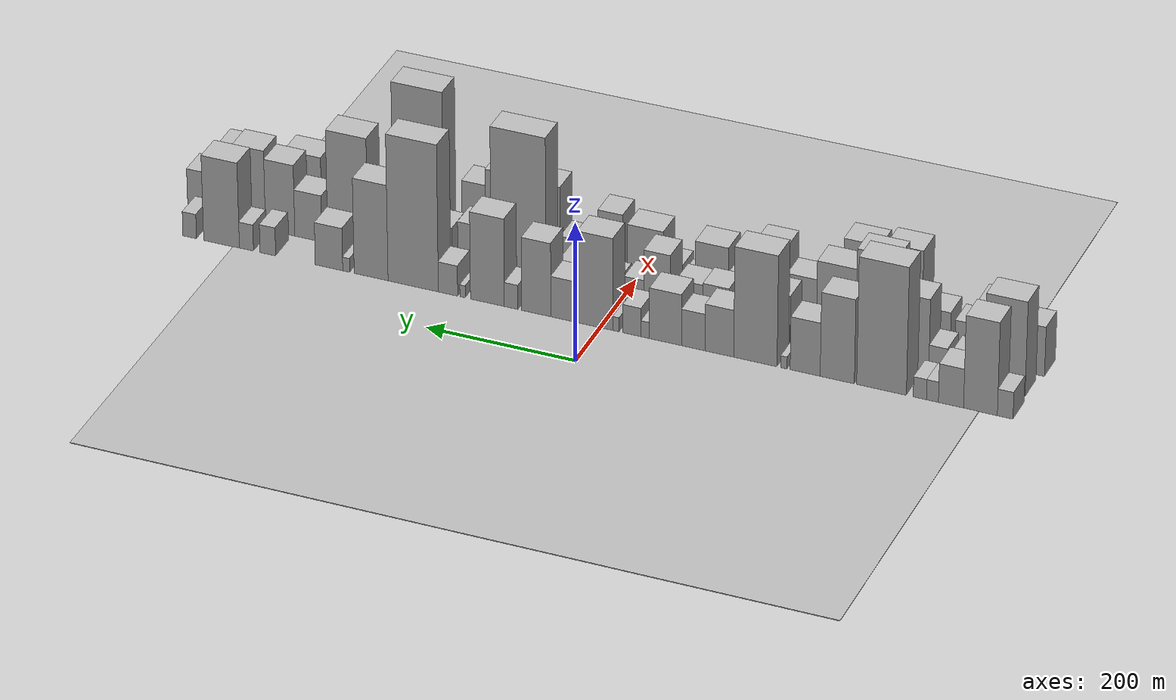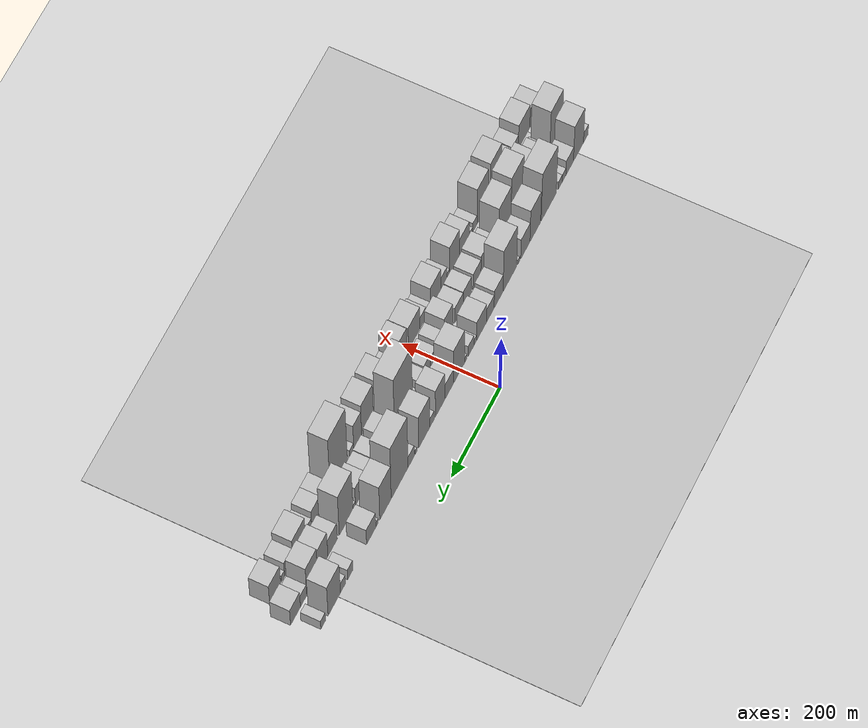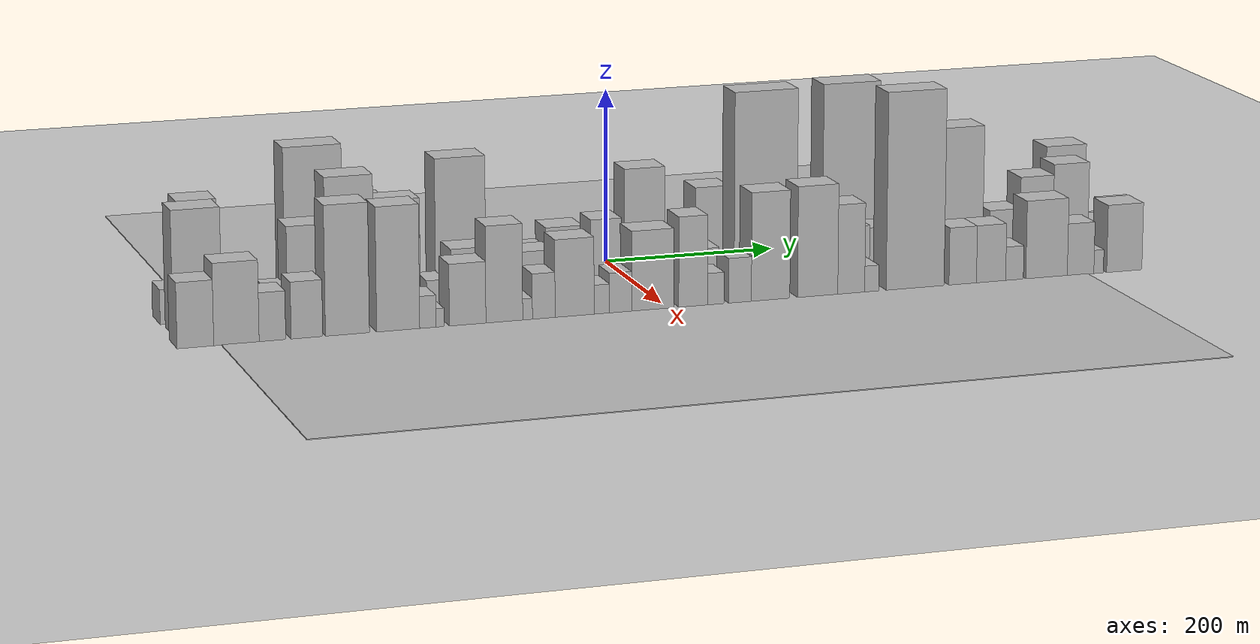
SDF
<?xml version="1.0" encoding="utf-8"?>

<sdf version="1.6">

   <world name="default">

      <gui fullscreen="0">

         <camera name="user_camera">

            <pose>-15 0 4.57585 0 0 0</pose>

            <view_controller>orbit</view_controller>

         </camera>

      </gui>

      <scene>

         <sky>

           <clouds>

             <speed>12</speed>

           </clouds>

         </sky>

         <ambient>0.4 0.4 0.4 1</ambient>

         <background>0.7 0.7 0.7 1</background>

         <shadows>1</shadows>

      </scene>

      <gravity>0 0 -9.8066</gravity>

      <magnetic_field>6e-06 2.3e-05 -4.2e-05</magnetic_field>

      <physics default="0" name="default_physics" type="ode">

         <ode>

            <solver>

               <type>quick</type>

               <iters>10</iters>

               <sor>1.0</sor>

               <use_dynamic_moi_rescaling>0</use_dynamic_moi_rescaling>

            </solver>

            <constraints>

               <cfm>0</cfm>

               <erp>0.2</erp>

               <contact_max_correcting_vel>100</contact_max_correcting_vel>

               <contact_surface_layer>0.001</contact_surface_layer>

            </constraints>

         </ode>

         <max_step_size>0.004</max_step_size>

         <real_time_factor>1</real_time_factor>

         <real_time_update_rate>250</real_time_update_rate>

      </physics>

      <light name="sun" type="directional">

         <cast_shadows>1</cast_shadows>

         <pose>0 0 10 0 0 0</pose>

         <diffuse>0.8 0.8 0.8 1</diffuse>

         <specular>0.2 0.2 0.2 1</specular>

         <attenuation>

            <range>1000</range>

            <constant>0.9</constant>

            <linear>0.01</linear>

            <quadratic>0.001</quadratic>

         </attenuation>

         <direction>-0.5 0.1 -0.9</direction>

      </light>

      <include>

         <name>ground_plane_1</name>

         <uri>model://HANNAS_ground_plane</uri>

         <pose>0 0 0  0 0 0</pose>

      </include>

      <include>

         <name>ground_plane_2</name>

         <uri>model://HANNAS_ground_plane</uri>

         <pose>100 0 0  0 0 0</pose>

      </include>

      <model name="building_1">

         <static>1</static>

         <pose frame="">100.0000 -533.8357 0 0.000000 0.000000 0.000000</pose>

         <link name="link">

            <pose frame="">0 0 19.50 0 0 0</pose>

            <collision name="collision">

               <geometry>

                  <box>

                     <size>40.0000 20.3287 39.0000</size>

                  </box>

               </geometry>

               <max_contacts>10</max_contacts>

               <surface>

                  <contact>

                     <ode/>

                  </contact>

                  <bounce/>

                  <friction>

                     <torsional>

                        <ode/>

                     </torsional>

                     <ode/>

                  </friction>

               </surface>

            </collision>

            <visual name="visual">

               <cast_shadows>0</cast_shadows>

               <geometry>

                  <box>

                     <size>40.0000 20.3287 39.0000</size>

                  </box>

               </geometry>

               <material>

                  <script>

                     <uri>model://HANNAS_wall/materials/scripts</uri>

                     <uri>model://HANNAS_wall/materials/textures</uri>

                     <name>vrc/HANNAS_wall</name>

                  </script>

               </material>

            </visual>

            <self_collide>0</self_collide>

            <enable_wind>0</enable_wind>

            <kinematic>0</kinematic>

         </link>

      </model>

      <model name="building_2">

         <static>1</static>

         <pose frame="">100.0000 -501.7357 0 0.000000 0.000000 0.000000</pose>

         <link name="link">

            <pose frame="">0 0 67.50 0 0 0</pose>

            <collision name="collision">

               <geometry>

                  <box>

                     <size>40.0000 43.8712 135.0000</size>

                  </box>

               </geometry>

               <max_contacts>10</max_contacts>

               <surface>

                  <contact>

                     <ode/>

                  </contact>

                  <bounce/>

                  <friction>

                     <torsional>

                        <ode/>

                     </torsional>

                     <ode/>

                  </friction>

               </surface>

            </collision>

            <visual name="visual">

               <cast_shadows>0</cast_shadows>

               <geometry>

                  <box>

                     <size>40.0000 43.8712 135.0000</size>

                  </box>

               </geometry>

               <material>

                  <script>

                     <uri>model://HANNAS_wall/materials/scripts</uri>

                     <uri>model://HANNAS_wall/materials/textures</uri>

                     <name>vrc/HANNAS_wall</name>

                  </script>

               </material>

            </visual>

            <self_collide>0</self_collide>

            <enable_wind>0</enable_wind>

            <kinematic>0</kinematic>

         </link>

      </model>

      <model name="building_3">

         <static>1</static>

         <pose frame="">100.0000 -463.4330 0 0.000000 0.000000 0.000000</pose>

         <link name="link">

            <pose frame="">0 0 28.50 0 0 0</pose>

            <collision name="collision">

               <geometry>

                  <box>

                     <size>40.0000 32.7341 57.0000</size>

                  </box>

               </geometry>

               <max_contacts>10</max_contacts>

               <surface>

                  <contact>

                     <ode/>

                  </contact>

                  <bounce/>

                  <friction>

                     <torsional>

                        <ode/>

                     </torsional>

                     <ode/>

                  </friction>

               </surface>

            </collision>

            <visual name="visual">

               <cast_shadows>0</cast_shadows>

               <geometry>

                  <box>

                     <size>40.0000 32.7341 57.0000</size>

                  </box>

               </geometry>

               <material>

                  <script>

                     <uri>model://HANNAS_wall/materials/scripts</uri>

                     <uri>model://HANNAS_wall/materials/textures</uri>

                     <name>vrc/HANNAS_wall</name>

                  </script>

               </material>

            </visual>

            <self_collide>0</self_collide>

            <enable_wind>0</enable_wind>

            <kinematic>0</kinematic>

         </link>

      </model>

      <model name="building_4">

         <static>1</static>

         <pose frame="">100.0000 -439.2820 0 0.000000 0.000000 0.000000</pose>

         <link name="link">

            <pose frame="">0 0 15.00 0 0 0</pose>

            <collision name="collision">

               <geometry>

                  <box>

                     <size>40.0000 15.5680 30.0000</size>

                  </box>

               </geometry>

               <max_contacts>10</max_contacts>

               <surface>

                  <contact>

                     <ode/>

                  </contact>

                  <bounce/>

                  <friction>

                     <torsional>

                        <ode/>

                     </torsional>

                     <ode/>

                  </friction>

               </surface>

            </collision>

            <visual name="visual">

               <cast_shadows>0</cast_shadows>

               <geometry>

                  <box>

                     <size>40.0000 15.5680 30.0000</size>

                  </box>

               </geometry>

               <material>

                  <script>

                     <uri>model://HANNAS_wall/materials/scripts</uri>

                     <uri>model://HANNAS_wall/materials/textures</uri>

                     <name>vrc/HANNAS_wall</name>

                  </script>

               </material>

            </visual>

            <self_collide>0</self_collide>

            <enable_wind>0</enable_wind>

            <kinematic>0</kinematic>

         </link>

      </model>

      <model name="building_5">

         <static>1</static>

         <pose frame="">100.0000 -422.9092 0 0.000000 0.000000 0.000000</pose>

         <link name="link">

            <pose frame="">0 0 15.00 0 0 0</pose>

            <collision name="collision">

               <geometry>

                  <box>

                     <size>40.0000 17.1775 30.0000</size>

                  </box>

               </geometry>

               <max_contacts>10</max_contacts>

               <surface>

                  <contact>

                     <ode/>

                  </contact>

                  <bounce/>

                  <friction>

                     <torsional>

                        <ode/>

                     </torsional>

                     <ode/>

                  </friction>

               </surface>

            </collision>

            <visual name="visual">

               <cast_shadows>0</cast_shadows>

               <geometry>

                  <box>

                     <size>40.0000 17.1775 30.0000</size>

                  </box>

               </geometry>

               <material>

                  <script>

                     <uri>model://HANNAS_wall/materials/scripts</uri>

                     <uri>model://HANNAS_wall/materials/textures</uri>

                     <name>vrc/HANNAS_wall</name>

                  </script>

               </material>

            </visual>

            <self_collide>0</self_collide>

            <enable_wind>0</enable_wind>

            <kinematic>0</kinematic>

         </link>

      </model>

      <model name="building_6">

         <static>1</static>

         <pose frame="">100.0000 -372.7456 0 0.000000 0.000000 0.000000</pose>

         <link name="link">

            <pose frame="">0 0 93.00 0 0 0</pose>

            <collision name="collision">

               <geometry>

                  <box>

                     <size>40.0000 65.1498 186.0000</size>

                  </box>

               </geometry>

               <max_contacts>10</max_contacts>

               <surface>

                  <contact>

                     <ode/>

                  </contact>

                  <bounce/>

                  <friction>

                     <torsional>

                        <ode/>

                     </torsional>

                     <ode/>

                  </friction>

               </surface>

            </collision>

            <visual name="visual">

               <cast_shadows>0</cast_shadows>

               <geometry>

                  <box>

                     <size>40.0000 65.1498 186.0000</size>

                  </box>

               </geometry>

               <material>

                  <script>

                     <uri>model://HANNAS_wall/materials/scripts</uri>

                     <uri>model://HANNAS_wall/materials/textures</uri>

                     <name>vrc/HANNAS_wall</name>

                  </script>

               </material>

            </visual>

            <self_collide>0</self_collide>

            <enable_wind>0</enable_wind>

            <kinematic>0</kinematic>

         </link>

      </model>

      <model name="building_7">

         <static>1</static>

         <pose frame="">100.0000 -314.7158 0 0.000000 0.000000 0.000000</pose>

         <link name="link">

            <pose frame="">0 0 61.50 0 0 0</pose>

            <collision name="collision">

               <geometry>

                  <box>

                     <size>40.0000 44.9099 123.0000</size>

                  </box>

               </geometry>

               <max_contacts>10</max_contacts>

               <surface>

                  <contact>

                     <ode/>

                  </contact>

                  <bounce/>

                  <friction>

                     <torsional>

                        <ode/>

                     </torsional>

                     <ode/>

                  </friction>

               </surface>

            </collision>

            <visual name="visual">

               <cast_shadows>0</cast_shadows>

               <geometry>

                  <box>

                     <size>40.0000 44.9099 123.0000</size>

                  </box>

               </geometry>

               <material>

                  <script>

                     <uri>model://HANNAS_wall/materials/scripts</uri>

                     <uri>model://HANNAS_wall/materials/textures</uri>

                     <name>vrc/HANNAS_wall</name>

                  </script>

               </material>

            </visual>

            <self_collide>0</self_collide>

            <enable_wind>0</enable_wind>

            <kinematic>0</kinematic>

         </link>

      </model>

      <model name="building_8">

         <static>1</static>

         <pose frame="">100.0000 -272.4738 0 0.000000 0.000000 0.000000</pose>

         <link name="link">

            <pose frame="">0 0 39.00 0 0 0</pose>

            <collision name="collision">

               <geometry>

                  <box>

                     <size>40.0000 39.5740 78.0000</size>

                  </box>

               </geometry>

               <max_contacts>10</max_contacts>

               <surface>

                  <contact>

                     <ode/>

                  </contact>

                  <bounce/>

                  <friction>

                     <torsional>

                        <ode/>

                     </torsional>

                     <ode/>

                  </friction>

               </surface>

            </collision>

            <visual name="visual">

               <cast_shadows>0</cast_shadows>

               <geometry>

                  <box>

                     <size>40.0000 39.5740 78.0000</size>

                  </box>

               </geometry>

               <material>

                  <script>

                     <uri>model://HANNAS_wall/materials/scripts</uri>

                     <uri>model://HANNAS_wall/materials/textures</uri>

                     <name>vrc/HANNAS_wall</name>

                  </script>

               </material>

            </visual>

            <self_collide>0</self_collide>

            <enable_wind>0</enable_wind>

            <kinematic>0</kinematic>

         </link>

      </model>

      <model name="building_9">

         <static>1</static>

         <pose frame="">100.0000 -244.5368 0 0.000000 0.000000 0.000000</pose>

         <link name="link">

            <pose frame="">0 0 9.00 0 0 0</pose>

            <collision name="collision">

               <geometry>

                  <box>

                     <size>40.0000 8.2999 18.0000</size>

                  </box>

               </geometry>

               <max_contacts>10</max_contacts>

               <surface>

                  <contact>

                     <ode/>

                  </contact>

                  <bounce/>

                  <friction>

                     <torsional>

                        <ode/>

                     </torsional>

                     <ode/>

                  </friction>

               </surface>

            </collision>

            <visual name="visual">

               <cast_shadows>0</cast_shadows>

               <geometry>

                  <box>

                     <size>40.0000 8.2999 18.0000</size>

                  </box>

               </geometry>

               <material>

                  <script>

                     <uri>model://HANNAS_wall/materials/scripts</uri>

                     <uri>model://HANNAS_wall/materials/textures</uri>

                     <name>vrc/HANNAS_wall</name>

                  </script>

               </material>

            </visual>

            <self_collide>0</self_collide>

            <enable_wind>0</enable_wind>

            <kinematic>0</kinematic>

         </link>

      </model>

      <model name="building_10">

         <static>1</static>

         <pose frame="">100.0000 -206.7228 0 0.000000 0.000000 0.000000</pose>

         <link name="link">

            <pose frame="">0 0 81.00 0 0 0</pose>

            <collision name="collision">

               <geometry>

                  <box>

                     <size>40.0000 57.3281 162.0000</size>

                  </box>

               </geometry>

               <max_contacts>10</max_contacts>

               <surface>

                  <contact>

                     <ode/>

                  </contact>

                  <bounce/>

                  <friction>

                     <torsional>

                        <ode/>

                     </torsional>

                     <ode/>

                  </friction>

               </surface>

            </collision>

            <visual name="visual">

               <cast_shadows>0</cast_shadows>

               <geometry>

                  <box>

                     <size>40.0000 57.3281 162.0000</size>

                  </box>

               </geometry>

               <material>

                  <script>

                     <uri>model://HANNAS_wall/materials/scripts</uri>

                     <uri>model://HANNAS_wall/materials/textures</uri>

                     <name>vrc/HANNAS_wall</name>

                  </script>

               </material>

            </visual>

            <self_collide>0</self_collide>

            <enable_wind>0</enable_wind>

            <kinematic>0</kinematic>

         </link>

      </model>

      <model name="building_11">

         <static>1</static>

         <pose frame="">100.0000 -158.9652 0 0.000000 0.000000 0.000000</pose>

         <link name="link">

            <pose frame="">0 0 34.50 0 0 0</pose>

            <collision name="collision">

               <geometry>

                  <box>

                     <size>40.0000 38.1870 69.0000</size>

                  </box>

               </geometry>

               <max_contacts>10</max_contacts>

               <surface>

                  <contact>

                     <ode/>

                  </contact>

                  <bounce/>

                  <friction>

                     <torsional>

                        <ode/>

                     </torsional>

                     <ode/>

                  </friction>

               </surface>

            </collision>

            <visual name="visual">

               <cast_shadows>0</cast_shadows>

               <geometry>

                  <box>

                     <size>40.0000 38.1870 69.0000</size>

                  </box>

               </geometry>

               <material>

                  <script>

                     <uri>model://HANNAS_wall/materials/scripts</uri>

                     <uri>model://HANNAS_wall/materials/textures</uri>

                     <name>vrc/HANNAS_wall</name>

                  </script>

               </material>

            </visual>

            <self_collide>0</self_collide>

            <enable_wind>0</enable_wind>

            <kinematic>0</kinematic>

         </link>

      </model>

      <model name="building_12">

         <static>1</static>

         <pose frame="">100.0000 -124.1919 0 0.000000 0.000000 0.000000</pose>

         <link name="link">

            <pose frame="">0 0 27.00 0 0 0</pose>

            <collision name="collision">

               <geometry>

                  <box>

                     <size>40.0000 31.3597 54.0000</size>

                  </box>

               </geometry>

               <max_contacts>10</max_contacts>

               <surface>

                  <contact>

                     <ode/>

                  </contact>

                  <bounce/>

                  <friction>

                     <torsional>

                        <ode/>

                     </torsional>

                     <ode/>

                  </friction>

               </surface>

            </collision>

            <visual name="visual">

               <cast_shadows>0</cast_shadows>

               <geometry>

                  <box>

                     <size>40.0000 31.3597 54.0000</size>

                  </box>

               </geometry>

               <material>

                  <script>

                     <uri>model://HANNAS_wall/materials/scripts</uri>

                     <uri>model://HANNAS_wall/materials/textures</uri>

                     <name>vrc/HANNAS_wall</name>

                  </script>

               </material>

            </visual>

            <self_collide>0</self_collide>

            <enable_wind>0</enable_wind>

            <kinematic>0</kinematic>

         </link>

      </model>

      <model name="building_13">

         <static>1</static>

         <pose frame="">100.0000 -87.1841 0 0.000000 0.000000 0.000000</pose>

         <link name="link">

            <pose frame="">0 0 37.50 0 0 0</pose>

            <collision name="collision">

               <geometry>

                  <box>

                     <size>40.0000 42.6557 75.0000</size>

                  </box>

               </geometry>

               <max_contacts>10</max_contacts>

               <surface>

                  <contact>

                     <ode/>

                  </contact>

                  <bounce/>

                  <friction>

                     <torsional>

                        <ode/>

                     </torsional>

                     <ode/>

                  </friction>

               </surface>

            </collision>

            <visual name="visual">

               <cast_shadows>0</cast_shadows>

               <geometry>

                  <box>

                     <size>40.0000 42.6557 75.0000</size>

                  </box>

               </geometry>

               <material>

                  <script>

                     <uri>model://HANNAS_wall/materials/scripts</uri>

                     <uri>model://HANNAS_wall/materials/textures</uri>

                     <name>vrc/HANNAS_wall</name>

                  </script>

               </material>

            </visual>

            <self_collide>0</self_collide>

            <enable_wind>0</enable_wind>

            <kinematic>0</kinematic>

         </link>

      </model>

      <model name="building_14">

         <static>1</static>

         <pose frame="">100.0000 -60.2784 0 0.000000 0.000000 0.000000</pose>

         <link name="link">

            <pose frame="">0 0 12.00 0 0 0</pose>

            <collision name="collision">

               <geometry>

                  <box>

                     <size>40.0000 11.1557 24.0000</size>

                  </box>

               </geometry>

               <max_contacts>10</max_contacts>

               <surface>

                  <contact>

                     <ode/>

                  </contact>

                  <bounce/>

                  <friction>

                     <torsional>

                        <ode/>

                     </torsional>

                     <ode/>

                  </friction>

               </surface>

            </collision>

            <visual name="visual">

               <cast_shadows>0</cast_shadows>

               <geometry>

                  <box>

                     <size>40.0000 11.1557 24.0000</size>

                  </box>

               </geometry>

               <material>

                  <script>

                     <uri>model://HANNAS_wall/materials/scripts</uri>

                     <uri>model://HANNAS_wall/materials/textures</uri>

                     <name>vrc/HANNAS_wall</name>

                  </script>

               </material>

            </visual>

            <self_collide>0</self_collide>

            <enable_wind>0</enable_wind>

            <kinematic>0</kinematic>

         </link>

      </model>

      <model name="building_15">

         <static>1</static>

         <pose frame="">100.0000 -42.5767 0 0.000000 0.000000 0.000000</pose>

         <link name="link">

            <pose frame="">0 0 21.00 0 0 0</pose>

            <collision name="collision">

               <geometry>

                  <box>

                     <size>40.0000 24.2479 42.0000</size>

                  </box>

               </geometry>

               <max_contacts>10</max_contacts>

               <surface>

                  <contact>

                     <ode/>

                  </contact>

                  <bounce/>

                  <friction>

                     <torsional>

                        <ode/>

                     </torsional>

                     <ode/>

                  </friction>

               </surface>

            </collision>

            <visual name="visual">

               <cast_shadows>0</cast_shadows>

               <geometry>

                  <box>

                     <size>40.0000 24.2479 42.0000</size>

                  </box>

               </geometry>

               <material>

                  <script>

                     <uri>model://HANNAS_wall/materials/scripts</uri>

                     <uri>model://HANNAS_wall/materials/textures</uri>

                     <name>vrc/HANNAS_wall</name>

                  </script>

               </material>

            </visual>

            <self_collide>0</self_collide>

            <enable_wind>0</enable_wind>

            <kinematic>0</kinematic>

         </link>

      </model>

      <model name="building_16">

         <static>1</static>

         <pose frame="">100.0000 -21.1023 0 0.000000 0.000000 0.000000</pose>

         <link name="link">

            <pose frame="">0 0 10.50 0 0 0</pose>

            <collision name="collision">

               <geometry>

                  <box>

                     <size>40.0000 8.7009 21.0000</size>

                  </box>

               </geometry>

               <max_contacts>10</max_contacts>

               <surface>

                  <contact>

                     <ode/>

                  </contact>

                  <bounce/>

                  <friction>

                     <torsional>

                        <ode/>

                     </torsional>

                     <ode/>

                  </friction>

               </surface>

            </collision>

            <visual name="visual">

               <cast_shadows>0</cast_shadows>

               <geometry>

                  <box>

                     <size>40.0000 8.7009 21.0000</size>

                  </box>

               </geometry>

               <material>

                  <script>

                     <uri>model://HANNAS_wall/materials/scripts</uri>

                     <uri>model://HANNAS_wall/materials/textures</uri>

                     <name>vrc/HANNAS_wall</name>

                  </script>

               </material>

            </visual>

            <self_collide>0</self_collide>

            <enable_wind>0</enable_wind>

            <kinematic>0</kinematic>

         </link>

      </model>

      <model name="building_17">

         <static>1</static>

         <pose frame="">100.0000 6.9142 0 0.000000 0.000000 0.000000</pose>

         <link name="link">

            <pose frame="">0 0 67.50 0 0 0</pose>

            <collision name="collision">

               <geometry>

                  <box>

                     <size>40.0000 47.3320 135.0000</size>

                  </box>

               </geometry>

               <max_contacts>10</max_contacts>

               <surface>

                  <contact>

                     <ode/>

                  </contact>

                  <bounce/>

                  <friction>

                     <torsional>

                        <ode/>

                     </torsional>

                     <ode/>

                  </friction>

               </surface>

            </collision>

            <visual name="visual">

               <cast_shadows>0</cast_shadows>

               <geometry>

                  <box>

                     <size>40.0000 47.3320 135.0000</size>

                  </box>

               </geometry>

               <material>

                  <script>

                     <uri>model://HANNAS_wall/materials/scripts</uri>

                     <uri>model://HANNAS_wall/materials/textures</uri>

                     <name>vrc/HANNAS_wall</name>

                  </script>

               </material>

            </visual>

            <self_collide>0</self_collide>

            <enable_wind>0</enable_wind>

            <kinematic>0</kinematic>

         </link>

      </model>

      <model name="building_18">

         <static>1</static>

         <pose frame="">100.0000 48.4592 0 0.000000 0.000000 0.000000</pose>

         <link name="link">

            <pose frame="">0 0 30.00 0 0 0</pose>

            <collision name="collision">

               <geometry>

                  <box>

                     <size>40.0000 35.7579 60.0000</size>

                  </box>

               </geometry>

               <max_contacts>10</max_contacts>

               <surface>

                  <contact>

                     <ode/>

                  </contact>

                  <bounce/>

                  <friction>

                     <torsional>

                        <ode/>

                     </torsional>

                     <ode/>

                  </friction>

               </surface>

            </collision>

            <visual name="visual">

               <cast_shadows>0</cast_shadows>

               <geometry>

                  <box>

                     <size>40.0000 35.7579 60.0000</size>

                  </box>

               </geometry>

               <material>

                  <script>

                     <uri>model://HANNAS_wall/materials/scripts</uri>

                     <uri>model://HANNAS_wall/materials/textures</uri>

                     <name>vrc/HANNAS_wall</name>

                  </script>

               </material>

            </visual>

            <self_collide>0</self_collide>

            <enable_wind>0</enable_wind>

            <kinematic>0</kinematic>

         </link>

      </model>

      <model name="building_19">

         <static>1</static>

         <pose frame="">100.0000 85.9648 0 0.000000 0.000000 0.000000</pose>

         <link name="link">

            <pose frame="">0 0 54.00 0 0 0</pose>

            <collision name="collision">

               <geometry>

                  <box>

                     <size>40.0000 39.2534 108.0000</size>

                  </box>

               </geometry>

               <max_contacts>10</max_contacts>

               <surface>

                  <contact>

                     <ode/>

                  </contact>

                  <bounce/>

                  <friction>

                     <torsional>

                        <ode/>

                     </torsional>

                     <ode/>

                  </friction>

               </surface>

            </collision>

            <visual name="visual">

               <cast_shadows>0</cast_shadows>

               <geometry>

                  <box>

                     <size>40.0000 39.2534 108.0000</size>

                  </box>

               </geometry>

               <material>

                  <script>

                     <uri>model://HANNAS_wall/materials/scripts</uri>

                     <uri>model://HANNAS_wall/materials/textures</uri>

                     <name>vrc/HANNAS_wall</name>

                  </script>

               </material>

            </visual>

            <self_collide>0</self_collide>

            <enable_wind>0</enable_wind>

            <kinematic>0</kinematic>

         </link>

      </model>

      <model name="building_20">

         <static>1</static>

         <pose frame="">100.0000 119.7995 0 0.000000 0.000000 0.000000</pose>

         <link name="link">

            <pose frame="">0 0 18.00 0 0 0</pose>

            <collision name="collision">

               <geometry>

                  <box>

                     <size>40.0000 18.4160 36.0000</size>

                  </box>

               </geometry>

               <max_contacts>10</max_contacts>

               <surface>

                  <contact>

                     <ode/>

                  </contact>

                  <bounce/>

                  <friction>

                     <torsional>

                        <ode/>

                     </torsional>

                     <ode/>

                  </friction>

               </surface>

            </collision>

            <visual name="visual">

               <cast_shadows>0</cast_shadows>

               <geometry>

                  <box>

                     <size>40.0000 18.4160 36.0000</size>

                  </box>

               </geometry>

               <material>

                  <script>

                     <uri>model://HANNAS_wall/materials/scripts</uri>

                     <uri>model://HANNAS_wall/materials/textures</uri>

                     <name>vrc/HANNAS_wall</name>

                  </script>

               </material>

            </visual>

            <self_collide>0</self_collide>

            <enable_wind>0</enable_wind>

            <kinematic>0</kinematic>

         </link>

      </model>

      <model name="building_21">

         <static>1</static>

         <pose frame="">100.0000 151.9927 0 0.000000 0.000000 0.000000</pose>

         <link name="link">

            <pose frame="">0 0 64.50 0 0 0</pose>

            <collision name="collision">

               <geometry>

                  <box>

                     <size>40.0000 45.9705 129.0000</size>

                  </box>

               </geometry>

               <max_contacts>10</max_contacts>

               <surface>

                  <contact>

                     <ode/>

                  </contact>

                  <bounce/>

                  <friction>

                     <torsional>

                        <ode/>

                     </torsional>

                     <ode/>

                  </friction>

               </surface>

            </collision>

            <visual name="visual">

               <cast_shadows>0</cast_shadows>

               <geometry>

                  <box>

                     <size>40.0000 45.9705 129.0000</size>

                  </box>

               </geometry>

               <material>

                  <script>

                     <uri>model://HANNAS_wall/materials/scripts</uri>

                     <uri>model://HANNAS_wall/materials/textures</uri>

                     <name>vrc/HANNAS_wall</name>

                  </script>

               </material>

            </visual>

            <self_collide>0</self_collide>

            <enable_wind>0</enable_wind>

            <kinematic>0</kinematic>

         </link>

      </model>

      <model name="building_22">

         <static>1</static>

         <pose frame="">100.0000 185.6658 0 0.000000 0.000000 0.000000</pose>

         <link name="link">

            <pose frame="">0 0 9.00 0 0 0</pose>

            <collision name="collision">

               <geometry>

                  <box>

                     <size>40.0000 7.3758 18.0000</size>

                  </box>

               </geometry>

               <max_contacts>10</max_contacts>

               <surface>

                  <contact>

                     <ode/>

                  </contact>

                  <bounce/>

                  <friction>

                     <torsional>

                        <ode/>

                     </torsional>

                     <ode/>

                  </friction>

               </surface>

            </collision>

            <visual name="visual">

               <cast_shadows>0</cast_shadows>

               <geometry>

                  <box>

                     <size>40.0000 7.3758 18.0000</size>

                  </box>

               </geometry>

               <material>

                  <script>

                     <uri>model://HANNAS_wall/materials/scripts</uri>

                     <uri>model://HANNAS_wall/materials/textures</uri>

                     <name>vrc/HANNAS_wall</name>

                  </script>

               </material>

            </visual>

            <self_collide>0</self_collide>

            <enable_wind>0</enable_wind>

            <kinematic>0</kinematic>

         </link>

      </model>

      <model name="building_23">

         <static>1</static>

         <pose frame="">100.0000 205.4401 0 0.000000 0.000000 0.000000</pose>

         <link name="link">

            <pose frame="">0 0 22.50 0 0 0</pose>

            <collision name="collision">

               <geometry>

                  <box>

                     <size>40.0000 26.1728 45.0000</size>

                  </box>

               </geometry>

               <max_contacts>10</max_contacts>

               <surface>

                  <contact>

                     <ode/>

                  </contact>

                  <bounce/>

                  <friction>

                     <torsional>

                        <ode/>

                     </torsional>

                     <ode/>

                  </friction>

               </surface>

            </collision>

            <visual name="visual">

               <cast_shadows>0</cast_shadows>

               <geometry>

                  <box>

                     <size>40.0000 26.1728 45.0000</size>

                  </box>

               </geometry>

               <material>

                  <script>

                     <uri>model://HANNAS_wall/materials/scripts</uri>

                     <uri>model://HANNAS_wall/materials/textures</uri>

                     <name>vrc/HANNAS_wall</name>

                  </script>

               </material>

            </visual>

            <self_collide>0</self_collide>

            <enable_wind>0</enable_wind>

            <kinematic>0</kinematic>

         </link>

      </model>

      <model name="building_24">

         <static>1</static>

         <pose frame="">100.0000 252.8469 0 0.000000 0.000000 0.000000</pose>

         <link name="link">

            <pose frame="">0 0 108.00 0 0 0</pose>

            <collision name="collision">

               <geometry>

                  <box>

                     <size>40.0000 68.6407 216.0000</size>

                  </box>

               </geometry>

               <max_contacts>10</max_contacts>

               <surface>

                  <contact>

                     <ode/>

                  </contact>

                  <bounce/>

                  <friction>

                     <torsional>

                        <ode/>

                     </torsional>

                     <ode/>

                  </friction>

               </surface>

            </collision>

            <visual name="visual">

               <cast_shadows>0</cast_shadows>

               <geometry>

                  <box>

                     <size>40.0000 68.6407 216.0000</size>

                  </box>

               </geometry>

               <material>

                  <script>

                     <uri>model://HANNAS_wall/materials/scripts</uri>

                     <uri>model://HANNAS_wall/materials/textures</uri>

                     <name>vrc/HANNAS_wall</name>

                  </script>

               </material>

            </visual>

            <self_collide>0</self_collide>

            <enable_wind>0</enable_wind>

            <kinematic>0</kinematic>

         </link>

      </model>

      <model name="building_25">

         <static>1</static>

         <pose frame="">100.0000 310.3236 0 0.000000 0.000000 0.000000</pose>

         <link name="link">

            <pose frame="">0 0 70.50 0 0 0</pose>

            <collision name="collision">

               <geometry>

                  <box>

                     <size>40.0000 46.3127 141.0000</size>

                  </box>

               </geometry>

               <max_contacts>10</max_contacts>

               <surface>

                  <contact>

                     <ode/>

                  </contact>

                  <bounce/>

                  <friction>

                     <torsional>

                        <ode/>

                     </torsional>

                     <ode/>

                  </friction>

               </surface>

            </collision>

            <visual name="visual">

               <cast_shadows>0</cast_shadows>

               <geometry>

                  <box>

                     <size>40.0000 46.3127 141.0000</size>

                  </box>

               </geometry>

               <material>

                  <script>

                     <uri>model://HANNAS_wall/materials/scripts</uri>

                     <uri>model://HANNAS_wall/materials/textures</uri>

                     <name>vrc/HANNAS_wall</name>

                  </script>

               </material>

            </visual>

            <self_collide>0</self_collide>

            <enable_wind>0</enable_wind>

            <kinematic>0</kinematic>

         </link>

      </model>

      <model name="building_26">

         <static>1</static>

         <pose frame="">100.0000 344.3438 0 0.000000 0.000000 0.000000</pose>

         <link name="link">

            <pose frame="">0 0 10.50 0 0 0</pose>

            <collision name="collision">

               <geometry>

                  <box>

                     <size>40.0000 9.7277 21.0000</size>

                  </box>

               </geometry>

               <max_contacts>10</max_contacts>

               <surface>

                  <contact>

                     <ode/>

                  </contact>

                  <bounce/>

                  <friction>

                     <torsional>

                        <ode/>

                     </torsional>

                     <ode/>

                  </friction>

               </surface>

            </collision>

            <visual name="visual">

               <cast_shadows>0</cast_shadows>

               <geometry>

                  <box>

                     <size>40.0000 9.7277 21.0000</size>

                  </box>

               </geometry>

               <material>

                  <script>

                     <uri>model://HANNAS_wall/materials/scripts</uri>

                     <uri>model://HANNAS_wall/materials/textures</uri>

                     <name>vrc/HANNAS_wall</name>

                  </script>

               </material>

            </visual>

            <self_collide>0</self_collide>

            <enable_wind>0</enable_wind>

            <kinematic>0</kinematic>

         </link>

      </model>

      <model name="building_27">

         <static>1</static>

         <pose frame="">100.0000 368.0430 0 0.000000 0.000000 0.000000</pose>

         <link name="link">

            <pose frame="">0 0 31.50 0 0 0</pose>

            <collision name="collision">

               <geometry>

                  <box>

                     <size>40.0000 37.6707 63.0000</size>

                  </box>

               </geometry>

               <max_contacts>10</max_contacts>

               <surface>

                  <contact>

                     <ode/>

                  </contact>

                  <bounce/>

                  <friction>

                     <torsional>

                        <ode/>

                     </torsional>

                     <ode/>

                  </friction>

               </surface>

            </collision>

            <visual name="visual">

               <cast_shadows>0</cast_shadows>

               <geometry>

                  <box>

                     <size>40.0000 37.6707 63.0000</size>

                  </box>

               </geometry>

               <material>

                  <script>

                     <uri>model://HANNAS_wall/materials/scripts</uri>

                     <uri>model://HANNAS_wall/materials/textures</uri>

                     <name>vrc/HANNAS_wall</name>

                  </script>

               </material>

            </visual>

            <self_collide>0</self_collide>

            <enable_wind>0</enable_wind>

            <kinematic>0</kinematic>

         </link>

      </model>

      <model name="building_28">

         <static>1</static>

         <pose frame="">100.0000 452.2449 0 0.000000 0.000000 0.000000</pose>

         <link name="link">

            <pose frame="">0 0 21.00 0 0 0</pose>

            <collision name="collision">

               <geometry>

                  <box>

                     <size>40.0000 21.5777 42.0000</size>

                  </box>

               </geometry>

               <max_contacts>10</max_contacts>

               <surface>

                  <contact>

                     <ode/>

                  </contact>

                  <bounce/>

                  <friction>

                     <torsional>

                        <ode/>

                     </torsional>

                     <ode/>

                  </friction>

               </surface>

            </collision>

            <visual name="visual">

               <cast_shadows>0</cast_shadows>

               <geometry>

                  <box>

                     <size>40.0000 21.5777 42.0000</size>

                  </box>

               </geometry>

               <material>

                  <script>

                     <uri>model://HANNAS_wall/materials/scripts</uri>

                     <uri>model://HANNAS_wall/materials/textures</uri>

                     <name>vrc/HANNAS_wall</name>

                  </script>

               </material>

            </visual>

            <self_collide>0</self_collide>

            <enable_wind>0</enable_wind>

            <kinematic>0</kinematic>

         </link>

      </model>

      <model name="building_29">

         <static>1</static>

         <pose frame="">100.0000 481.7919 0 0.000000 0.000000 0.000000</pose>

         <link name="link">

            <pose frame="">0 0 19.50 0 0 0</pose>

            <collision name="collision">

               <geometry>

                  <box>

                     <size>40.0000 19.5164 39.0000</size>

                  </box>

               </geometry>

               <max_contacts>10</max_contacts>

               <surface>

                  <contact>

                     <ode/>

                  </contact>

                  <bounce/>

                  <friction>

                     <torsional>

                        <ode/>

                     </torsional>

                     <ode/>

                  </friction>

               </surface>

            </collision>

            <visual name="visual">

               <cast_shadows>0</cast_shadows>

               <geometry>

                  <box>

                     <size>40.0000 19.5164 39.0000</size>

                  </box>

               </geometry>

               <material>

                  <script>

                     <uri>model://HANNAS_wall/materials/scripts</uri>

                     <uri>model://HANNAS_wall/materials/textures</uri>

                     <name>vrc/HANNAS_wall</name>

                  </script>

               </material>

            </visual>

            <self_collide>0</self_collide>

            <enable_wind>0</enable_wind>

            <kinematic>0</kinematic>

         </link>

      </model>

      <model name="building_30">

         <static>1</static>

         <pose frame="">100.0000 516.3029 0 0.000000 0.000000 0.000000</pose>

         <link name="link">

            <pose frame="">0 0 63.00 0 0 0</pose>

            <collision name="collision">

               <geometry>

                  <box>

                     <size>40.0000 49.5057 126.0000</size>

                  </box>

               </geometry>

               <max_contacts>10</max_contacts>

               <surface>

                  <contact>

                     <ode/>

                  </contact>

                  <bounce/>

                  <friction>

                     <torsional>

                        <ode/>

                     </torsional>

                     <ode/>

                  </friction>

               </surface>

            </collision>

            <visual name="visual">

               <cast_shadows>0</cast_shadows>

               <geometry>

                  <box>

                     <size>40.0000 49.5057 126.0000</size>

                  </box>

               </geometry>

               <material>

                  <script>

                     <uri>model://HANNAS_wall/materials/scripts</uri>

                     <uri>model://HANNAS_wall/materials/textures</uri>

                     <name>vrc/HANNAS_wall</name>

                  </script>

               </material>

            </visual>

            <self_collide>0</self_collide>

            <enable_wind>0</enable_wind>

            <kinematic>0</kinematic>

         </link>

      </model>

      <model name="building_31">

         <static>1</static>

         <pose frame="">100.0000 560.4568 0 0.000000 0.000000 0.000000</pose>

         <link name="link">

            <pose frame="">0 0 18.00 0 0 0</pose>

            <collision name="collision">

               <geometry>

                  <box>

                     <size>40.0000 18.8020 36.0000</size>

                  </box>

               </geometry>

               <max_contacts>10</max_contacts>

               <surface>

                  <contact>

                     <ode/>

                  </contact>

                  <bounce/>

                  <friction>

                     <torsional>

                        <ode/>

                     </torsional>

                     <ode/>

                  </friction>

               </surface>

            </collision>

            <visual name="visual">

               <cast_shadows>0</cast_shadows>

               <geometry>

                  <box>

                     <size>40.0000 18.8020 36.0000</size>

                  </box>

               </geometry>

               <material>

                  <script>

                     <uri>model://HANNAS_wall/materials/scripts</uri>

                     <uri>model://HANNAS_wall/materials/textures</uri>

                     <name>vrc/HANNAS_wall</name>

                  </script>

               </material>

            </visual>

            <self_collide>0</self_collide>

            <enable_wind>0</enable_wind>

            <kinematic>0</kinematic>

         </link>

      </model>

      <model name="building_32">

         <static>1</static>

         <pose frame="">152.0000 -514.2317 0 0.000000 0.000000 0.000000</pose>

         <link name="link">

            <pose frame="">0 0 69.00 0 0 0</pose>

            <collision name="collision">

               <geometry>

                  <box>

                     <size>40.0000 53.5365 138.0000</size>

                  </box>

               </geometry>

               <max_contacts>10</max_contacts>

               <surface>

                  <contact>

                     <ode/>

                  </contact>

                  <bounce/>

                  <friction>

                     <torsional>

                        <ode/>

                     </torsional>

                     <ode/>

                  </friction>

               </surface>

            </collision>

            <visual name="visual">

               <cast_shadows>0</cast_shadows>

               <geometry>

                  <box>

                     <size>40.0000 53.5365 138.0000</size>

                  </box>

               </geometry>

               <material>

                  <script>

                     <uri>model://HANNAS_wall/materials/scripts</uri>

                     <uri>model://HANNAS_wall/materials/textures</uri>

                     <name>vrc/HANNAS_wall</name>

                  </script>

               </material>

            </visual>

            <self_collide>0</self_collide>

            <enable_wind>0</enable_wind>

            <kinematic>0</kinematic>

         </link>

      </model>

      <model name="building_33">

         <static>1</static>

         <pose frame="">152.0000 -473.0222 0 0.000000 0.000000 0.000000</pose>

         <link name="link">

            <pose frame="">0 0 13.50 0 0 0</pose>

            <collision name="collision">

               <geometry>

                  <box>

                     <size>40.0000 10.8826 27.0000</size>

                  </box>

               </geometry>

               <max_contacts>10</max_contacts>

               <surface>

                  <contact>

                     <ode/>

                  </contact>

                  <bounce/>

                  <friction>

                     <torsional>

                        <ode/>

                     </torsional>

                     <ode/>

                  </friction>

               </surface>

            </collision>

            <visual name="visual">

               <cast_shadows>0</cast_shadows>

               <geometry>

                  <box>

                     <size>40.0000 10.8826 27.0000</size>

                  </box>

               </geometry>

               <material>

                  <script>

                     <uri>model://HANNAS_wall/materials/scripts</uri>

                     <uri>model://HANNAS_wall/materials/textures</uri>

                     <name>vrc/HANNAS_wall</name>

                  </script>

               </material>

            </visual>

            <self_collide>0</self_collide>

            <enable_wind>0</enable_wind>

            <kinematic>0</kinematic>

         </link>

      </model>

      <model name="building_34">

         <static>1</static>

         <pose frame="">152.0000 -455.8984 0 0.000000 0.000000 0.000000</pose>

         <link name="link">

            <pose frame="">0 0 21.00 0 0 0</pose>

            <collision name="collision">

               <geometry>

                  <box>

                     <size>40.0000 23.3649 42.0000</size>

                  </box>

               </geometry>

               <max_contacts>10</max_contacts>

               <surface>

                  <contact>

                     <ode/>

                  </contact>

                  <bounce/>

                  <friction>

                     <torsional>

                        <ode/>

                     </torsional>

                     <ode/>

                  </friction>

               </surface>

            </collision>

            <visual name="visual">

               <cast_shadows>0</cast_shadows>

               <geometry>

                  <box>

                     <size>40.0000 23.3649 42.0000</size>

                  </box>

               </geometry>

               <material>

                  <script>

                     <uri>model://HANNAS_wall/materials/scripts</uri>

                     <uri>model://HANNAS_wall/materials/textures</uri>

                     <name>vrc/HANNAS_wall</name>

                  </script>

               </material>

            </visual>

            <self_collide>0</self_collide>

            <enable_wind>0</enable_wind>

            <kinematic>0</kinematic>

         </link>

      </model>

      <model name="building_35">

         <static>1</static>

         <pose frame="">152.0000 -427.2207 0 0.000000 0.000000 0.000000</pose>

         <link name="link">

            <pose frame="">0 0 22.50 0 0 0</pose>

            <collision name="collision">

               <geometry>

                  <box>

                     <size>40.0000 23.9904 45.0000</size>

                  </box>

               </geometry>

               <max_contacts>10</max_contacts>

               <surface>

                  <contact>

                     <ode/>

                  </contact>

                  <bounce/>

                  <friction>

                     <torsional>

                        <ode/>

                     </torsional>

                     <ode/>

                  </friction>

               </surface>

            </collision>

            <visual name="visual">

               <cast_shadows>0</cast_shadows>

               <geometry>

                  <box>

                     <size>40.0000 23.9904 45.0000</size>

                  </box>

               </geometry>

               <material>

                  <script>

                     <uri>model://HANNAS_wall/materials/scripts</uri>

                     <uri>model://HANNAS_wall/materials/textures</uri>

                     <name>vrc/HANNAS_wall</name>

                  </script>

               </material>

            </visual>

            <self_collide>0</self_collide>

            <enable_wind>0</enable_wind>

            <kinematic>0</kinematic>

         </link>

      </model>

      <model name="building_36">

         <static>1</static>

         <pose frame="">152.0000 -394.1154 0 0.000000 0.000000 0.000000</pose>

         <link name="link">

            <pose frame="">0 0 55.50 0 0 0</pose>

            <collision name="collision">

               <geometry>

                  <box>

                     <size>40.0000 42.2202 111.0000</size>

                  </box>

               </geometry>

               <max_contacts>10</max_contacts>

               <surface>

                  <contact>

                     <ode/>

                  </contact>

                  <bounce/>

                  <friction>

                     <torsional>

                        <ode/>

                     </torsional>

                     <ode/>

                  </friction>

               </surface>

            </collision>

            <visual name="visual">

               <cast_shadows>0</cast_shadows>

               <geometry>

                  <box>

                     <size>40.0000 42.2202 111.0000</size>

                  </box>

               </geometry>

               <material>

                  <script>

                     <uri>model://HANNAS_wall/materials/scripts</uri>

                     <uri>model://HANNAS_wall/materials/textures</uri>

                     <name>vrc/HANNAS_wall</name>

                  </script>

               </material>

            </visual>

            <self_collide>0</self_collide>

            <enable_wind>0</enable_wind>

            <kinematic>0</kinematic>

         </link>

      </model>

      <model name="building_37">

         <static>1</static>

         <pose frame="">152.0000 -346.0021 0 0.000000 0.000000 0.000000</pose>

         <link name="link">

            <pose frame="">0 0 81.00 0 0 0</pose>

            <collision name="collision">

               <geometry>

                  <box>

                     <size>40.0000 54.0065 162.0000</size>

                  </box>

               </geometry>

               <max_contacts>10</max_contacts>

               <surface>

                  <contact>

                     <ode/>

                  </contact>

                  <bounce/>

                  <friction>

                     <torsional>

                        <ode/>

                     </torsional>

                     <ode/>

                  </friction>

               </surface>

            </collision>

            <visual name="visual">

               <cast_shadows>0</cast_shadows>

               <geometry>

                  <box>

                     <size>40.0000 54.0065 162.0000</size>

                  </box>

               </geometry>

               <material>

                  <script>

                     <uri>model://HANNAS_wall/materials/scripts</uri>

                     <uri>model://HANNAS_wall/materials/textures</uri>

                     <name>vrc/HANNAS_wall</name>

                  </script>

               </material>

            </visual>

            <self_collide>0</self_collide>

            <enable_wind>0</enable_wind>

            <kinematic>0</kinematic>

         </link>

      </model>

      <model name="building_38">

         <static>1</static>

         <pose frame="">152.0000 -292.9950 0 0.000000 0.000000 0.000000</pose>

         <link name="link">

            <pose frame="">0 0 66.00 0 0 0</pose>

            <collision name="collision">

               <geometry>

                  <box>

                     <size>40.0000 52.0078 132.0000</size>

                  </box>

               </geometry>

               <max_contacts>10</max_contacts>

               <surface>

                  <contact>

                     <ode/>

                  </contact>

                  <bounce/>

                  <friction>

                     <torsional>

                        <ode/>

                     </torsional>

                     <ode/>

                  </friction>

               </surface>

            </collision>

            <visual name="visual">

               <cast_shadows>0</cast_shadows>

               <geometry>

                  <box>

                     <size>40.0000 52.0078 132.0000</size>

                  </box>

               </geometry>

               <material>

                  <script>

                     <uri>model://HANNAS_wall/materials/scripts</uri>

                     <uri>model://HANNAS_wall/materials/textures</uri>

                     <name>vrc/HANNAS_wall</name>

                  </script>

               </material>

            </visual>

            <self_collide>0</self_collide>

            <enable_wind>0</enable_wind>

            <kinematic>0</kinematic>

         </link>

      </model>

      <model name="building_39">

         <static>1</static>

         <pose frame="">152.0000 -249.2636 0 0.000000 0.000000 0.000000</pose>

         <link name="link">

            <pose frame="">0 0 19.50 0 0 0</pose>

            <collision name="collision">

               <geometry>

                  <box>

                     <size>40.0000 21.4550 39.0000</size>

                  </box>

               </geometry>

               <max_contacts>10</max_contacts>

               <surface>

                  <contact>

                     <ode/>

                  </contact>

                  <bounce/>

                  <friction>

                     <torsional>

                        <ode/>

                     </torsional>

                     <ode/>

                  </friction>

               </surface>

            </collision>

            <visual name="visual">

               <cast_shadows>0</cast_shadows>

               <geometry>

                  <box>

                     <size>40.0000 21.4550 39.0000</size>

                  </box>

               </geometry>

               <material>

                  <script>

                     <uri>model://HANNAS_wall/materials/scripts</uri>

                     <uri>model://HANNAS_wall/materials/textures</uri>

                     <name>vrc/HANNAS_wall</name>

                  </script>

               </material>

            </visual>

            <self_collide>0</self_collide>

            <enable_wind>0</enable_wind>

            <kinematic>0</kinematic>

         </link>

      </model>

      <model name="building_40">

         <static>1</static>

         <pose frame="">152.0000 -212.0736 0 0.000000 0.000000 0.000000</pose>

         <link name="link">

            <pose frame="">0 0 36.00 0 0 0</pose>

            <collision name="collision">

               <geometry>

                  <box>

                     <size>40.0000 40.9250 72.0000</size>

                  </box>

               </geometry>

               <max_contacts>10</max_contacts>

               <surface>

                  <contact>

                     <ode/>

                  </contact>

                  <bounce/>

                  <friction>

                     <torsional>

                        <ode/>

                     </torsional>

                     <ode/>

                  </friction>

               </surface>

            </collision>

            <visual name="visual">

               <cast_shadows>0</cast_shadows>

               <geometry>

                  <box>

                     <size>40.0000 40.9250 72.0000</size>

                  </box>

               </geometry>

               <material>

                  <script>

                     <uri>model://HANNAS_wall/materials/scripts</uri>

                     <uri>model://HANNAS_wall/materials/textures</uri>

                     <name>vrc/HANNAS_wall</name>

                  </script>

               </material>

            </visual>

            <self_collide>0</self_collide>

            <enable_wind>0</enable_wind>

            <kinematic>0</kinematic>

         </link>

      </model>

      <model name="building_41">

         <static>1</static>

         <pose frame="">152.0000 -174.9117 0 0.000000 0.000000 0.000000</pose>

         <link name="link">

            <pose frame="">0 0 30.00 0 0 0</pose>

            <collision name="collision">

               <geometry>

                  <box>

                     <size>40.0000 33.3990 60.0000</size>

                  </box>

               </geometry>

               <max_contacts>10</max_contacts>

               <surface>

                  <contact>

                     <ode/>

                  </contact>

                  <bounce/>

                  <friction>

                     <torsional>

                        <ode/>

                     </torsional>

                     <ode/>

                  </friction>

               </surface>

            </collision>

            <visual name="visual">

               <cast_shadows>0</cast_shadows>

               <geometry>

                  <box>

                     <size>40.0000 33.3990 60.0000</size>

                  </box>

               </geometry>

               <material>

                  <script>

                     <uri>model://HANNAS_wall/materials/scripts</uri>

                     <uri>model://HANNAS_wall/materials/textures</uri>

                     <name>vrc/HANNAS_wall</name>

                  </script>

               </material>

            </visual>

            <self_collide>0</self_collide>

            <enable_wind>0</enable_wind>

            <kinematic>0</kinematic>

         </link>

      </model>

      <model name="building_42">

         <static>1</static>

         <pose frame="">152.0000 -133.7987 0 0.000000 0.000000 0.000000</pose>

         <link name="link">

            <pose frame="">0 0 31.50 0 0 0</pose>

            <collision name="collision">

               <geometry>

                  <box>

                     <size>40.0000 34.8270 63.0000</size>

                  </box>

               </geometry>

               <max_contacts>10</max_contacts>

               <surface>

                  <contact>

                     <ode/>

                  </contact>

                  <bounce/>

                  <friction>

                     <torsional>

                        <ode/>

                     </torsional>

                     <ode/>

                  </friction>

               </surface>

            </collision>

            <visual name="visual">

               <cast_shadows>0</cast_shadows>

               <geometry>

                  <box>

                     <size>40.0000 34.8270 63.0000</size>

                  </box>

               </geometry>

               <material>

                  <script>

                     <uri>model://HANNAS_wall/materials/scripts</uri>

                     <uri>model://HANNAS_wall/materials/textures</uri>

                     <name>vrc/HANNAS_wall</name>

                  </script>

               </material>

            </visual>

            <self_collide>0</self_collide>

            <enable_wind>0</enable_wind>

            <kinematic>0</kinematic>

         </link>

      </model>

      <model name="building_43">

         <static>1</static>

         <pose frame="">152.0000 -98.5936 0 0.000000 0.000000 0.000000</pose>

         <link name="link">

            <pose frame="">0 0 30.00 0 0 0</pose>

            <collision name="collision">

               <geometry>

                  <box>

                     <size>40.0000 35.5831 60.0000</size>

                  </box>

               </geometry>

               <max_contacts>10</max_contacts>

               <surface>

                  <contact>

                     <ode/>

                  </contact>

                  <bounce/>

                  <friction>

                     <torsional>

                        <ode/>

                     </torsional>

                     <ode/>

                  </friction>

               </surface>

            </collision>

            <visual name="visual">

               <cast_shadows>0</cast_shadows>

               <geometry>

                  <box>

                     <size>40.0000 35.5831 60.0000</size>

                  </box>

               </geometry>

               <material>

                  <script>

                     <uri>model://HANNAS_wall/materials/scripts</uri>

                     <uri>model://HANNAS_wall/materials/textures</uri>

                     <name>vrc/HANNAS_wall</name>

                  </script>

               </material>

            </visual>

            <self_collide>0</self_collide>

            <enable_wind>0</enable_wind>

            <kinematic>0</kinematic>

         </link>

      </model>

      <model name="building_44">

         <static>1</static>

         <pose frame="">152.0000 -55.0811 0 0.000000 0.000000 0.000000</pose>

         <link name="link">

            <pose frame="">0 0 46.50 0 0 0</pose>

            <collision name="collision">

               <geometry>

                  <box>

                     <size>40.0000 35.4419 93.0000</size>

                  </box>

               </geometry>

               <max_contacts>10</max_contacts>

               <surface>

                  <contact>

                     <ode/>

                  </contact>

                  <bounce/>

                  <friction>

                     <torsional>

                        <ode/>

                     </torsional>

                     <ode/>

                  </friction>

               </surface>

            </collision>

            <visual name="visual">

               <cast_shadows>0</cast_shadows>

               <geometry>

                  <box>

                     <size>40.0000 35.4419 93.0000</size>

                  </box>

               </geometry>

               <material>

                  <script>

                     <uri>model://HANNAS_wall/materials/scripts</uri>

                     <uri>model://HANNAS_wall/materials/textures</uri>

                     <name>vrc/HANNAS_wall</name>

                  </script>

               </material>

            </visual>

            <self_collide>0</self_collide>

            <enable_wind>0</enable_wind>

            <kinematic>0</kinematic>

         </link>

      </model>

      <model name="building_45">

         <static>1</static>

         <pose frame="">152.0000 -24.2012 0 0.000000 0.000000 0.000000</pose>

         <link name="link">

            <pose frame="">0 0 24.00 0 0 0</pose>

            <collision name="collision">

               <geometry>

                  <box>

                     <size>40.0000 26.3179 48.0000</size>

                  </box>

               </geometry>

               <max_contacts>10</max_contacts>

               <surface>

                  <contact>

                     <ode/>

                  </contact>

                  <bounce/>

                  <friction>

                     <torsional>

                        <ode/>

                     </torsional>

                     <ode/>

                  </friction>

               </surface>

            </collision>

            <visual name="visual">

               <cast_shadows>0</cast_shadows>

               <geometry>

                  <box>

                     <size>40.0000 26.3179 48.0000</size>

                  </box>

               </geometry>

               <material>

                  <script>

                     <uri>model://HANNAS_wall/materials/scripts</uri>

                     <uri>model://HANNAS_wall/materials/textures</uri>

                     <name>vrc/HANNAS_wall</name>

                  </script>

               </material>

            </visual>

            <self_collide>0</self_collide>

            <enable_wind>0</enable_wind>

            <kinematic>0</kinematic>

         </link>

      </model>

      <model name="building_46">

         <static>1</static>

         <pose frame="">152.0000 7.0707 0 0.000000 0.000000 0.000000</pose>

         <link name="link">

            <pose frame="">0 0 21.00 0 0 0</pose>

            <collision name="collision">

               <geometry>

                  <box>

                     <size>40.0000 24.2258 42.0000</size>

                  </box>

               </geometry>

               <max_contacts>10</max_contacts>

               <surface>

                  <contact>

                     <ode/>

                  </contact>

                  <bounce/>

                  <friction>

                     <torsional>

                        <ode/>

                     </torsional>

                     <ode/>

                  </friction>

               </surface>

            </collision>

            <visual name="visual">

               <cast_shadows>0</cast_shadows>

               <geometry>

                  <box>

                     <size>40.0000 24.2258 42.0000</size>

                  </box>

               </geometry>

               <material>

                  <script>

                     <uri>model://HANNAS_wall/materials/scripts</uri>

                     <uri>model://HANNAS_wall/materials/textures</uri>

                     <name>vrc/HANNAS_wall</name>

                  </script>

               </material>

            </visual>

            <self_collide>0</self_collide>

            <enable_wind>0</enable_wind>

            <kinematic>0</kinematic>

         </link>

      </model>

      <model name="building_47">

         <static>1</static>

         <pose frame="">152.0000 33.6650 0 0.000000 0.000000 0.000000</pose>

         <link name="link">

            <pose frame="">0 0 28.50 0 0 0</pose>

            <collision name="collision">

               <geometry>

                  <box>

                     <size>40.0000 28.9629 57.0000</size>

                  </box>

               </geometry>

               <max_contacts>10</max_contacts>

               <surface>

                  <contact>

                     <ode/>

                  </contact>

                  <bounce/>

                  <friction>

                     <torsional>

                        <ode/>

                     </torsional>

                     <ode/>

                  </friction>

               </surface>

            </collision>

            <visual name="visual">

               <cast_shadows>0</cast_shadows>

               <geometry>

                  <box>

                     <size>40.0000 28.9629 57.0000</size>

                  </box>

               </geometry>

               <material>

                  <script>

                     <uri>model://HANNAS_wall/materials/scripts</uri>

                     <uri>model://HANNAS_wall/materials/textures</uri>

                     <name>vrc/HANNAS_wall</name>

                  </script>

               </material>

            </visual>

            <self_collide>0</self_collide>

            <enable_wind>0</enable_wind>

            <kinematic>0</kinematic>

         </link>

      </model>

      <model name="building_48">

         <static>1</static>

         <pose frame="">152.0000 62.4467 0 0.000000 0.000000 0.000000</pose>

         <link name="link">

            <pose frame="">0 0 25.50 0 0 0</pose>

            <collision name="collision">

               <geometry>

                  <box>

                     <size>40.0000 28.6006 51.0000</size>

                  </box>

               </geometry>

               <max_contacts>10</max_contacts>

               <surface>

                  <contact>

                     <ode/>

                  </contact>

                  <bounce/>

                  <friction>

                     <torsional>

                        <ode/>

                     </torsional>

                     <ode/>

                  </friction>

               </surface>

            </collision>

            <visual name="visual">

               <cast_shadows>0</cast_shadows>

               <geometry>

                  <box>

                     <size>40.0000 28.6006 51.0000</size>

                  </box>

               </geometry>

               <material>

                  <script>

                     <uri>model://HANNAS_wall/materials/scripts</uri>

                     <uri>model://HANNAS_wall/materials/textures</uri>

                     <name>vrc/HANNAS_wall</name>

                  </script>

               </material>

            </visual>

            <self_collide>0</self_collide>

            <enable_wind>0</enable_wind>

            <kinematic>0</kinematic>

         </link>

      </model>

      <model name="building_49">

         <static>1</static>

         <pose frame="">152.0000 80.5838 0 0.000000 0.000000 0.000000</pose>

         <link name="link">

            <pose frame="">0 0 9.00 0 0 0</pose>

            <collision name="collision">

               <geometry>

                  <box>

                     <size>40.0000 7.6736 18.0000</size>

                  </box>

               </geometry>

               <max_contacts>10</max_contacts>

               <surface>

                  <contact>

                     <ode/>

                  </contact>

                  <bounce/>

                  <friction>

                     <torsional>

                        <ode/>

                     </torsional>

                     <ode/>

                  </friction>

               </surface>

            </collision>

            <visual name="visual">

               <cast_shadows>0</cast_shadows>

               <geometry>

                  <box>

                     <size>40.0000 7.6736 18.0000</size>

                  </box>

               </geometry>

               <material>

                  <script>

                     <uri>model://HANNAS_wall/materials/scripts</uri>

                     <uri>model://HANNAS_wall/materials/textures</uri>

                     <name>vrc/HANNAS_wall</name>

                  </script>

               </material>

            </visual>

            <self_collide>0</self_collide>

            <enable_wind>0</enable_wind>

            <kinematic>0</kinematic>

         </link>

      </model>

      <model name="building_50">

         <static>1</static>

         <pose frame="">152.0000 131.5387 0 0.000000 0.000000 0.000000</pose>

         <link name="link">

            <pose frame="">0 0 112.50 0 0 0</pose>

            <collision name="collision">

               <geometry>

                  <box>

                     <size>40.0000 74.2363 225.0000</size>

                  </box>

               </geometry>

               <max_contacts>10</max_contacts>

               <surface>

                  <contact>

                     <ode/>

                  </contact>

                  <bounce/>

                  <friction>

                     <torsional>

                        <ode/>

                     </torsional>

                     <ode/>

                  </friction>

               </surface>

            </collision>

            <visual name="visual">

               <cast_shadows>0</cast_shadows>

               <geometry>

                  <box>

                     <size>40.0000 74.2363 225.0000</size>

                  </box>

               </geometry>

               <material>

                  <script>

                     <uri>model://HANNAS_wall/materials/scripts</uri>

                     <uri>model://HANNAS_wall/materials/textures</uri>

                     <name>vrc/HANNAS_wall</name>

                  </script>

               </material>

            </visual>

            <self_collide>0</self_collide>

            <enable_wind>0</enable_wind>

            <kinematic>0</kinematic>

         </link>

      </model>

      <model name="building_51">

         <static>1</static>

         <pose frame="">152.0000 194.2749 0 0.000000 0.000000 0.000000</pose>

         <link name="link">

            <pose frame="">0 0 37.50 0 0 0</pose>

            <collision name="collision">

               <geometry>

                  <box>

                     <size>40.0000 39.2360 75.0000</size>

                  </box>

               </geometry>

               <max_contacts>10</max_contacts>

               <surface>

                  <contact>

                     <ode/>

                  </contact>

                  <bounce/>

                  <friction>

                     <torsional>

                        <ode/>

                     </torsional>

                     <ode/>

                  </friction>

               </surface>

            </collision>

            <visual name="visual">

               <cast_shadows>0</cast_shadows>

               <geometry>

                  <box>

                     <size>40.0000 39.2360 75.0000</size>

                  </box>

               </geometry>

               <material>

                  <script>

                     <uri>model://HANNAS_wall/materials/scripts</uri>

                     <uri>model://HANNAS_wall/materials/textures</uri>

                     <name>vrc/HANNAS_wall</name>

                  </script>

               </material>

            </visual>

            <self_collide>0</self_collide>

            <enable_wind>0</enable_wind>

            <kinematic>0</kinematic>

         </link>

      </model>

      <model name="building_52">

         <static>1</static>

         <pose frame="">152.0000 238.6678 0 0.000000 0.000000 0.000000</pose>

         <link name="link">

            <pose frame="">0 0 31.50 0 0 0</pose>

            <collision name="collision">

               <geometry>

                  <box>

                     <size>40.0000 33.5497 63.0000</size>

                  </box>

               </geometry>

               <max_contacts>10</max_contacts>

               <surface>

                  <contact>

                     <ode/>

                  </contact>

                  <bounce/>

                  <friction>

                     <torsional>

                        <ode/>

                     </torsional>

                     <ode/>

                  </friction>

               </surface>

            </collision>

            <visual name="visual">

               <cast_shadows>0</cast_shadows>

               <geometry>

                  <box>

                     <size>40.0000 33.5497 63.0000</size>

                  </box>

               </geometry>

               <material>

                  <script>

                     <uri>model://HANNAS_wall/materials/scripts</uri>

                     <uri>model://HANNAS_wall/materials/textures</uri>

                     <name>vrc/HANNAS_wall</name>

                  </script>

               </material>

            </visual>

            <self_collide>0</self_collide>

            <enable_wind>0</enable_wind>

            <kinematic>0</kinematic>

         </link>

      </model>

      <model name="building_53">

         <static>1</static>

         <pose frame="">152.0000 271.9533 0 0.000000 0.000000 0.000000</pose>

         <link name="link">

            <pose frame="">0 0 30.00 0 0 0</pose>

            <collision name="collision">

               <geometry>

                  <box>

                     <size>40.0000 33.0214 60.0000</size>

                  </box>

               </geometry>

               <max_contacts>10</max_contacts>

               <surface>

                  <contact>

                     <ode/>

                  </contact>

                  <bounce/>

                  <friction>

                     <torsional>

                        <ode/>

                     </torsional>

                     <ode/>

                  </friction>

               </surface>

            </collision>

            <visual name="visual">

               <cast_shadows>0</cast_shadows>

               <geometry>

                  <box>

                     <size>40.0000 33.0214 60.0000</size>

                  </box>

               </geometry>

               <material>

                  <script>

                     <uri>model://HANNAS_wall/materials/scripts</uri>

                     <uri>model://HANNAS_wall/materials/textures</uri>

                     <name>vrc/HANNAS_wall</name>

                  </script>

               </material>

            </visual>

            <self_collide>0</self_collide>

            <enable_wind>0</enable_wind>

            <kinematic>0</kinematic>

         </link>

      </model>

      <model name="building_54">

         <static>1</static>

         <pose frame="">152.0000 307.9099 0 0.000000 0.000000 0.000000</pose>

         <link name="link">

            <pose frame="">0 0 37.50 0 0 0</pose>

            <collision name="collision">

               <geometry>

                  <box>

                     <size>40.0000 38.8918 75.0000</size>

                  </box>

               </geometry>

               <max_contacts>10</max_contacts>

               <surface>

                  <contact>

                     <ode/>

                  </contact>

                  <bounce/>

                  <friction>

                     <torsional>

                        <ode/>

                     </torsional>

                     <ode/>

                  </friction>

               </surface>

            </collision>

            <visual name="visual">

               <cast_shadows>0</cast_shadows>

               <geometry>

                  <box>

                     <size>40.0000 38.8918 75.0000</size>

                  </box>

               </geometry>

               <material>

                  <script>

                     <uri>model://HANNAS_wall/materials/scripts</uri>

                     <uri>model://HANNAS_wall/materials/textures</uri>

                     <name>vrc/HANNAS_wall</name>

                  </script>

               </material>

            </visual>

            <self_collide>0</self_collide>

            <enable_wind>0</enable_wind>

            <kinematic>0</kinematic>

         </link>

      </model>

      <model name="building_55">

         <static>1</static>

         <pose frame="">152.0000 332.2854 0 0.000000 0.000000 0.000000</pose>

         <link name="link">

            <pose frame="">0 0 10.50 0 0 0</pose>

            <collision name="collision">

               <geometry>

                  <box>

                     <size>40.0000 9.8590 21.0000</size>

                  </box>

               </geometry>

               <max_contacts>10</max_contacts>

               <surface>

                  <contact>

                     <ode/>

                  </contact>

                  <bounce/>

                  <friction>

                     <torsional>

                        <ode/>

                     </torsional>

                     <ode/>

                  </friction>

               </surface>

            </collision>

            <visual name="visual">

               <cast_shadows>0</cast_shadows>

               <geometry>

                  <box>

                     <size>40.0000 9.8590 21.0000</size>

                  </box>

               </geometry>

               <material>

                  <script>

                     <uri>model://HANNAS_wall/materials/scripts</uri>

                     <uri>model://HANNAS_wall/materials/textures</uri>

                     <name>vrc/HANNAS_wall</name>

                  </script>

               </material>

            </visual>

            <self_collide>0</self_collide>

            <enable_wind>0</enable_wind>

            <kinematic>0</kinematic>

         </link>

      </model>

      <model name="building_56">

         <static>1</static>

         <pose frame="">152.0000 364.8871 0 0.000000 0.000000 0.000000</pose>

         <link name="link">

            <pose frame="">0 0 84.00 0 0 0</pose>

            <collision name="collision">

               <geometry>

                  <box>

                     <size>40.0000 55.3444 168.0000</size>

                  </box>

               </geometry>

               <max_contacts>10</max_contacts>

               <surface>

                  <contact>

                     <ode/>

                  </contact>

                  <bounce/>

                  <friction>

                     <torsional>

                        <ode/>

                     </torsional>

                     <ode/>

                  </friction>

               </surface>

            </collision>

            <visual name="visual">

               <cast_shadows>0</cast_shadows>

               <geometry>

                  <box>

                     <size>40.0000 55.3444 168.0000</size>

                  </box>

               </geometry>

               <material>

                  <script>

                     <uri>model://HANNAS_wall/materials/scripts</uri>

                     <uri>model://HANNAS_wall/materials/textures</uri>

                     <name>vrc/HANNAS_wall</name>

                  </script>

               </material>

            </visual>

            <self_collide>0</self_collide>

            <enable_wind>0</enable_wind>

            <kinematic>0</kinematic>

         </link>

      </model>

      <model name="building_57">

         <static>1</static>

         <pose frame="">152.0000 419.3515 0 0.000000 0.000000 0.000000</pose>

         <link name="link">

            <pose frame="">0 0 34.50 0 0 0</pose>

            <collision name="collision">

               <geometry>

                  <box>

                     <size>40.0000 37.5845 69.0000</size>

                  </box>

               </geometry>

               <max_contacts>10</max_contacts>

               <surface>

                  <contact>

                     <ode/>

                  </contact>

                  <bounce/>

                  <friction>

                     <torsional>

                        <ode/>

                     </torsional>

                     <ode/>

                  </friction>

               </surface>

            </collision>

            <visual name="visual">

               <cast_shadows>0</cast_shadows>

               <geometry>

                  <box>

                     <size>40.0000 37.5845 69.0000</size>

                  </box>

               </geometry>

               <material>

                  <script>

                     <uri>model://HANNAS_wall/materials/scripts</uri>

                     <uri>model://HANNAS_wall/materials/textures</uri>

                     <name>vrc/HANNAS_wall</name>

                  </script>

               </material>

            </visual>

            <self_collide>0</self_collide>

            <enable_wind>0</enable_wind>

            <kinematic>0</kinematic>

         </link>

      </model>

      <model name="building_58">

         <static>1</static>

         <pose frame="">152.0000 458.4582 0 0.000000 0.000000 0.000000</pose>

         <link name="link">

            <pose frame="">0 0 52.50 0 0 0</pose>

            <collision name="collision">

               <geometry>

                  <box>

                     <size>40.0000 40.6289 105.0000</size>

                  </box>

               </geometry>

               <max_contacts>10</max_contacts>

               <surface>

                  <contact>

                     <ode/>

                  </contact>

                  <bounce/>

                  <friction>

                     <torsional>

                        <ode/>

                     </torsional>

                     <ode/>

                  </friction>

               </surface>

            </collision>

            <visual name="visual">

               <cast_shadows>0</cast_shadows>

               <geometry>

                  <box>

                     <size>40.0000 40.6289 105.0000</size>

                  </box>

               </geometry>

               <material>

                  <script>

                     <uri>model://HANNAS_wall/materials/scripts</uri>

                     <uri>model://HANNAS_wall/materials/textures</uri>

                     <name>vrc/HANNAS_wall</name>

                  </script>

               </material>

            </visual>

            <self_collide>0</self_collide>

            <enable_wind>0</enable_wind>

            <kinematic>0</kinematic>

         </link>

      </model>

      <model name="building_59">

         <static>1</static>

         <pose frame="">152.0000 500.4478 0 0.000000 0.000000 0.000000</pose>

         <link name="link">

            <pose frame="">0 0 58.50 0 0 0</pose>

            <collision name="collision">

               <geometry>

                  <box>

                     <size>40.0000 43.3503 117.0000</size>

                  </box>

               </geometry>

               <max_contacts>10</max_contacts>

               <surface>

                  <contact>

                     <ode/>

                  </contact>

                  <bounce/>

                  <friction>

                     <torsional>

                        <ode/>

                     </torsional>

                     <ode/>

                  </friction>

               </surface>

            </collision>

            <visual name="visual">

               <cast_shadows>0</cast_shadows>

               <geometry>

                  <box>

                     <size>40.0000 43.3503 117.0000</size>

                  </box>

               </geometry>

               <material>

                  <script>

                     <uri>model://HANNAS_wall/materials/scripts</uri>

                     <uri>model://HANNAS_wall/materials/textures</uri>

                     <name>vrc/HANNAS_wall</name>

                  </script>

               </material>

            </visual>

            <self_collide>0</self_collide>

            <enable_wind>0</enable_wind>

            <kinematic>0</kinematic>

         </link>

      </model>

      <model name="building_60">

         <static>1</static>

         <pose frame="">152.0000 534.8358 0 0.000000 0.000000 0.000000</pose>

         <link name="link">

            <pose frame="">0 0 24.00 0 0 0</pose>

            <collision name="collision">

               <geometry>

                  <box>

                     <size>40.0000 25.4257 48.0000</size>

                  </box>

               </geometry>

               <max_contacts>10</max_contacts>

               <surface>

                  <contact>

                     <ode/>

                  </contact>

                  <bounce/>

                  <friction>

                     <torsional>

                        <ode/>

                     </torsional>

                     <ode/>

                  </friction>

               </surface>

            </collision>

            <visual name="visual">

               <cast_shadows>0</cast_shadows>

               <geometry>

                  <box>

                     <size>40.0000 25.4257 48.0000</size>

                  </box>

               </geometry>

               <material>

                  <script>

                     <uri>model://HANNAS_wall/materials/scripts</uri>

                     <uri>model://HANNAS_wall/materials/textures</uri>

                     <name>vrc/HANNAS_wall</name>

                  </script>

               </material>

            </visual>

            <self_collide>0</self_collide>

            <enable_wind>0</enable_wind>

            <kinematic>0</kinematic>

         </link>

      </model>

      <model name="building_61">

         <static>1</static>

         <pose frame="">152.0000 567.1620 0 0.000000 0.000000 0.000000</pose>

         <link name="link">

            <pose frame="">0 0 33.00 0 0 0</pose>

            <collision name="collision">

               <geometry>

                  <box>

                     <size>40.0000 39.2267 66.0000</size>

                  </box>

               </geometry>

               <max_contacts>10</max_contacts>

               <surface>

                  <contact>

                     <ode/>

                  </contact>

                  <bounce/>

                  <friction>

                     <torsional>

                        <ode/>

                     </torsional>

                     <ode/>

                  </friction>

               </surface>

            </collision>

            <visual name="visual">

               <cast_shadows>0</cast_shadows>

               <geometry>

                  <box>

                     <size>40.0000 39.2267 66.0000</size>

                  </box>

               </geometry>

               <material>

                  <script>

                     <uri>model://HANNAS_wall/materials/scripts</uri>

                     <uri>model://HANNAS_wall/materials/textures</uri>

                     <name>vrc/HANNAS_wall</name>

                  </script>

               </material>

            </visual>

            <self_collide>0</self_collide>

            <enable_wind>0</enable_wind>

            <kinematic>0</kinematic>

         </link>

      </model>

      <model name="building_62">

         <static>1</static>

         <pose frame="">204.0000 -528.2205 0 0.000000 0.000000 0.000000</pose>

         <link name="link">

            <pose frame="">0 0 36.00 0 0 0</pose>

            <collision name="collision">

               <geometry>

                  <box>

                     <size>40.0000 39.5590 72.0000</size>

                  </box>

               </geometry>

               <max_contacts>10</max_contacts>

               <surface>

                  <contact>

                     <ode/>

                  </contact>

                  <bounce/>

                  <friction>

                     <torsional>

                        <ode/>

                     </torsional>

                     <ode/>

                  </friction>

               </surface>

            </collision>

            <visual name="visual">

               <cast_shadows>0</cast_shadows>

               <geometry>

                  <box>

                     <size>40.0000 39.5590 72.0000</size>

                  </box>

               </geometry>

               <material>

                  <script>

                     <uri>model://HANNAS_wall/materials/scripts</uri>

                     <uri>model://HANNAS_wall/materials/textures</uri>

                     <name>vrc/HANNAS_wall</name>

                  </script>

               </material>

            </visual>

            <self_collide>0</self_collide>

            <enable_wind>0</enable_wind>

            <kinematic>0</kinematic>

         </link>

      </model>

      <model name="building_63">

         <static>1</static>

         <pose frame="">204.0000 -483.7912 0 0.000000 0.000000 0.000000</pose>

         <link name="link">

            <pose frame="">0 0 45.00 0 0 0</pose>

            <collision name="collision">

               <geometry>

                  <box>

                     <size>40.0000 49.2997 90.0000</size>

                  </box>

               </geometry>

               <max_contacts>10</max_contacts>

               <surface>

                  <contact>

                     <ode/>

                  </contact>

                  <bounce/>

                  <friction>

                     <torsional>

                        <ode/>

                     </torsional>

                     <ode/>

                  </friction>

               </surface>

            </collision>

            <visual name="visual">

               <cast_shadows>0</cast_shadows>

               <geometry>

                  <box>

                     <size>40.0000 49.2997 90.0000</size>

                  </box>

               </geometry>

               <material>

                  <script>

                     <uri>model://HANNAS_wall/materials/scripts</uri>

                     <uri>model://HANNAS_wall/materials/textures</uri>

                     <name>vrc/HANNAS_wall</name>

                  </script>

               </material>

            </visual>

            <self_collide>0</self_collide>

            <enable_wind>0</enable_wind>

            <kinematic>0</kinematic>

         </link>

      </model>

      <model name="building_64">

         <static>1</static>

         <pose frame="">204.0000 -444.6662 0 0.000000 0.000000 0.000000</pose>

         <link name="link">

            <pose frame="">0 0 27.00 0 0 0</pose>

            <collision name="collision">

               <geometry>

                  <box>

                     <size>40.0000 28.9502 54.0000</size>

                  </box>

               </geometry>

               <max_contacts>10</max_contacts>

               <surface>

                  <contact>

                     <ode/>

                  </contact>

                  <bounce/>

                  <friction>

                     <torsional>

                        <ode/>

                     </torsional>

                     <ode/>

                  </friction>

               </surface>

            </collision>

            <visual name="visual">

               <cast_shadows>0</cast_shadows>

               <geometry>

                  <box>

                     <size>40.0000 28.9502 54.0000</size>

                  </box>

               </geometry>

               <material>

                  <script>

                     <uri>model://HANNAS_wall/materials/scripts</uri>

                     <uri>model://HANNAS_wall/materials/textures</uri>

                     <name>vrc/HANNAS_wall</name>

                  </script>

               </material>

            </visual>

            <self_collide>0</self_collide>

            <enable_wind>0</enable_wind>

            <kinematic>0</kinematic>

         </link>

      </model>

      <model name="building_65">

         <static>1</static>

         <pose frame="">204.0000 -406.9002 0 0.000000 0.000000 0.000000</pose>

         <link name="link">

            <pose frame="">0 0 31.50 0 0 0</pose>

            <collision name="collision">

               <geometry>

                  <box>

                     <size>40.0000 34.5819 63.0000</size>

                  </box>

               </geometry>

               <max_contacts>10</max_contacts>

               <surface>

                  <contact>

                     <ode/>

                  </contact>

                  <bounce/>

                  <friction>

                     <torsional>

                        <ode/>

                     </torsional>

                     <ode/>

                  </friction>

               </surface>

            </collision>

            <visual name="visual">

               <cast_shadows>0</cast_shadows>

               <geometry>

                  <box>

                     <size>40.0000 34.5819 63.0000</size>

                  </box>

               </geometry>

               <material>

                  <script>

                     <uri>model://HANNAS_wall/materials/scripts</uri>

                     <uri>model://HANNAS_wall/materials/textures</uri>

                     <name>vrc/HANNAS_wall</name>

                  </script>

               </material>

            </visual>

            <self_collide>0</self_collide>

            <enable_wind>0</enable_wind>

            <kinematic>0</kinematic>

         </link>

      </model>

      <model name="building_66">

         <static>1</static>

         <pose frame="">204.0000 -362.3307 0 0.000000 0.000000 0.000000</pose>

         <link name="link">

            <pose frame="">0 0 72.00 0 0 0</pose>

            <collision name="collision">

               <geometry>

                  <box>

                     <size>40.0000 48.5571 144.0000</size>

                  </box>

               </geometry>

               <max_contacts>10</max_contacts>

               <surface>

                  <contact>

                     <ode/>

                  </contact>

                  <bounce/>

                  <friction>

                     <torsional>

                        <ode/>

                     </torsional>

                     <ode/>

                  </friction>

               </surface>

            </collision>

            <visual name="visual">

               <cast_shadows>0</cast_shadows>

               <geometry>

                  <box>

                     <size>40.0000 48.5571 144.0000</size>

                  </box>

               </geometry>

               <material>

                  <script>

                     <uri>model://HANNAS_wall/materials/scripts</uri>

                     <uri>model://HANNAS_wall/materials/textures</uri>

                     <name>vrc/HANNAS_wall</name>

                  </script>

               </material>

            </visual>

            <self_collide>0</self_collide>

            <enable_wind>0</enable_wind>

            <kinematic>0</kinematic>

         </link>

      </model>

      <model name="building_67">

         <static>1</static>

         <pose frame="">204.0000 -306.1538 0 0.000000 0.000000 0.000000</pose>

         <link name="link">

            <pose frame="">0 0 69.00 0 0 0</pose>

            <collision name="collision">

               <geometry>

                  <box>

                     <size>40.0000 47.7966 138.0000</size>

                  </box>

               </geometry>

               <max_contacts>10</max_contacts>

               <surface>

                  <contact>

                     <ode/>

                  </contact>

                  <bounce/>

                  <friction>

                     <torsional>

                        <ode/>

                     </torsional>

                     <ode/>

                  </friction>

               </surface>

            </collision>

            <visual name="visual">

               <cast_shadows>0</cast_shadows>

               <geometry>

                  <box>

                     <size>40.0000 47.7966 138.0000</size>

                  </box>

               </geometry>

               <material>

                  <script>

                     <uri>model://HANNAS_wall/materials/scripts</uri>

                     <uri>model://HANNAS_wall/materials/textures</uri>

                     <name>vrc/HANNAS_wall</name>

                  </script>

               </material>

            </visual>

            <self_collide>0</self_collide>

            <enable_wind>0</enable_wind>

            <kinematic>0</kinematic>

         </link>

      </model>

      <model name="building_68">

         <static>1</static>

         <pose frame="">204.0000 -273.0487 0 0.000000 0.000000 0.000000</pose>

         <link name="link">

            <pose frame="">0 0 18.00 0 0 0</pose>

            <collision name="collision">

               <geometry>

                  <box>

                     <size>40.0000 18.4138 36.0000</size>

                  </box>

               </geometry>

               <max_contacts>10</max_contacts>

               <surface>

                  <contact>

                     <ode/>

                  </contact>

                  <bounce/>

                  <friction>

                     <torsional>

                        <ode/>

                     </torsional>

                     <ode/>

                  </friction>

               </surface>

            </collision>

            <visual name="visual">

               <cast_shadows>0</cast_shadows>

               <geometry>

                  <box>

                     <size>40.0000 18.4138 36.0000</size>

                  </box>

               </geometry>

               <material>

                  <script>

                     <uri>model://HANNAS_wall/materials/scripts</uri>

                     <uri>model://HANNAS_wall/materials/textures</uri>

                     <name>vrc/HANNAS_wall</name>

                  </script>

               </material>

            </visual>

            <self_collide>0</self_collide>

            <enable_wind>0</enable_wind>

            <kinematic>0</kinematic>

         </link>

      </model>

      <model name="building_69">

         <static>1</static>

         <pose frame="">204.0000 -259.4952 0 0.000000 0.000000 0.000000</pose>

         <link name="link">

            <pose frame="">0 0 10.50 0 0 0</pose>

            <collision name="collision">

               <geometry>

                  <box>

                     <size>40.0000 8.6932 21.0000</size>

                  </box>

               </geometry>

               <max_contacts>10</max_contacts>

               <surface>

                  <contact>

                     <ode/>

                  </contact>

                  <bounce/>

                  <friction>

                     <torsional>

                        <ode/>

                     </torsional>

                     <ode/>

                  </friction>

               </surface>

            </collision>

            <visual name="visual">

               <cast_shadows>0</cast_shadows>

               <geometry>

                  <box>

                     <size>40.0000 8.6932 21.0000</size>

                  </box>

               </geometry>

               <material>

                  <script>

                     <uri>model://HANNAS_wall/materials/scripts</uri>

                     <uri>model://HANNAS_wall/materials/textures</uri>

                     <name>vrc/HANNAS_wall</name>

                  </script>

               </material>

            </visual>

            <self_collide>0</self_collide>

            <enable_wind>0</enable_wind>

            <kinematic>0</kinematic>

         </link>

      </model>

      <model name="building_70">

         <static>1</static>

         <pose frame="">204.0000 -228.6432 0 0.000000 0.000000 0.000000</pose>

         <link name="link">

            <pose frame="">0 0 34.50 0 0 0</pose>

            <collision name="collision">

               <geometry>

                  <box>

                     <size>40.0000 41.0106 69.0000</size>

                  </box>

               </geometry>

               <max_contacts>10</max_contacts>

               <surface>

                  <contact>

                     <ode/>

                  </contact>

                  <bounce/>

                  <friction>

                     <torsional>

                        <ode/>

                     </torsional>

                     <ode/>

                  </friction>

               </surface>

            </collision>

            <visual name="visual">

               <cast_shadows>0</cast_shadows>

               <geometry>

                  <box>

                     <size>40.0000 41.0106 69.0000</size>

                  </box>

               </geometry>

               <material>

                  <script>

                     <uri>model://HANNAS_wall/materials/scripts</uri>

                     <uri>model://HANNAS_wall/materials/textures</uri>

                     <name>vrc/HANNAS_wall</name>

                  </script>

               </material>

            </visual>

            <self_collide>0</self_collide>

            <enable_wind>0</enable_wind>

            <kinematic>0</kinematic>

         </link>

      </model>

      <model name="building_71">

         <static>1</static>

         <pose frame="">204.0000 -187.3996 0 0.000000 0.000000 0.000000</pose>

         <link name="link">

            <pose frame="">0 0 54.00 0 0 0</pose>

            <collision name="collision">

               <geometry>

                  <box>

                     <size>40.0000 41.4765 108.0000</size>

                  </box>

               </geometry>

               <max_contacts>10</max_contacts>

               <surface>

                  <contact>

                     <ode/>

                  </contact>

                  <bounce/>

                  <friction>

                     <torsional>

                        <ode/>

                     </torsional>

                     <ode/>

                  </friction>

               </surface>

            </collision>

            <visual name="visual">

               <cast_shadows>0</cast_shadows>

               <geometry>

                  <box>

                     <size>40.0000 41.4765 108.0000</size>

                  </box>

               </geometry>

               <material>

                  <script>

                     <uri>model://HANNAS_wall/materials/scripts</uri>

                     <uri>model://HANNAS_wall/materials/textures</uri>

                     <name>vrc/HANNAS_wall</name>

                  </script>

               </material>

            </visual>

            <self_collide>0</self_collide>

            <enable_wind>0</enable_wind>

            <kinematic>0</kinematic>

         </link>

      </model>

      <model name="building_72">

         <static>1</static>

         <pose frame="">204.0000 -161.1612 0 0.000000 0.000000 0.000000</pose>

         <link name="link">

            <pose frame="">0 0 12.00 0 0 0</pose>

            <collision name="collision">

               <geometry>

                  <box>

                     <size>40.0000 11.0003 24.0000</size>

                  </box>

               </geometry>

               <max_contacts>10</max_contacts>

               <surface>

                  <contact>

                     <ode/>

                  </contact>

                  <bounce/>

                  <friction>

                     <torsional>

                        <ode/>

                     </torsional>

                     <ode/>

                  </friction>

               </surface>

            </collision>

            <visual name="visual">

               <cast_shadows>0</cast_shadows>

               <geometry>

                  <box>

                     <size>40.0000 11.0003 24.0000</size>

                  </box>

               </geometry>

               <material>

                  <script>

                     <uri>model://HANNAS_wall/materials/scripts</uri>

                     <uri>model://HANNAS_wall/materials/textures</uri>

                     <name>vrc/HANNAS_wall</name>

                  </script>

               </material>

            </visual>

            <self_collide>0</self_collide>

            <enable_wind>0</enable_wind>

            <kinematic>0</kinematic>

         </link>

      </model>

      <model name="building_73">

         <static>1</static>

         <pose frame="">204.0000 -142.8271 0 0.000000 0.000000 0.000000</pose>

         <link name="link">

            <pose frame="">0 0 25.50 0 0 0</pose>

            <collision name="collision">

               <geometry>

                  <box>

                     <size>40.0000 25.6680 51.0000</size>

                  </box>

               </geometry>

               <max_contacts>10</max_contacts>

               <surface>

                  <contact>

                     <ode/>

                  </contact>

                  <bounce/>

                  <friction>

                     <torsional>

                        <ode/>

                     </torsional>

                     <ode/>

                  </friction>

               </surface>

            </collision>

            <visual name="visual">

               <cast_shadows>0</cast_shadows>

               <geometry>

                  <box>

                     <size>40.0000 25.6680 51.0000</size>

                  </box>

               </geometry>

               <material>

                  <script>

                     <uri>model://HANNAS_wall/materials/scripts</uri>

                     <uri>model://HANNAS_wall/materials/textures</uri>

                     <name>vrc/HANNAS_wall</name>

                  </script>

               </material>

            </visual>

            <self_collide>0</self_collide>

            <enable_wind>0</enable_wind>

            <kinematic>0</kinematic>

         </link>

      </model>

      <model name="building_74">

         <static>1</static>

         <pose frame="">204.0000 -107.7701 0 0.000000 0.000000 0.000000</pose>

         <link name="link">

            <pose frame="">0 0 43.50 0 0 0</pose>

            <collision name="collision">

               <geometry>

                  <box>

                     <size>40.0000 44.4458 87.0000</size>

                  </box>

               </geometry>

               <max_contacts>10</max_contacts>

               <surface>

                  <contact>

                     <ode/>

                  </contact>

                  <bounce/>

                  <friction>

                     <torsional>

                        <ode/>

                     </torsional>

                     <ode/>

                  </friction>

               </surface>

            </collision>

            <visual name="visual">

               <cast_shadows>0</cast_shadows>

               <geometry>

                  <box>

                     <size>40.0000 44.4458 87.0000</size>

                  </box>

               </geometry>

               <material>

                  <script>

                     <uri>model://HANNAS_wall/materials/scripts</uri>

                     <uri>model://HANNAS_wall/materials/textures</uri>

                     <name>vrc/HANNAS_wall</name>

                  </script>

               </material>

            </visual>

            <self_collide>0</self_collide>

            <enable_wind>0</enable_wind>

            <kinematic>0</kinematic>

         </link>

      </model>

      <model name="building_75">

         <static>1</static>

         <pose frame="">204.0000 -76.6233 0 0.000000 0.000000 0.000000</pose>

         <link name="link">

            <pose frame="">0 0 16.50 0 0 0</pose>

            <collision name="collision">

               <geometry>

                  <box>

                     <size>40.0000 17.8479 33.0000</size>

                  </box>

               </geometry>

               <max_contacts>10</max_contacts>

               <surface>

                  <contact>

                     <ode/>

                  </contact>

                  <bounce/>

                  <friction>

                     <torsional>

                        <ode/>

                     </torsional>

                     <ode/>

                  </friction>

               </surface>

            </collision>

            <visual name="visual">

               <cast_shadows>0</cast_shadows>

               <geometry>

                  <box>

                     <size>40.0000 17.8479 33.0000</size>

                  </box>

               </geometry>

               <material>

                  <script>

                     <uri>model://HANNAS_wall/materials/scripts</uri>

                     <uri>model://HANNAS_wall/materials/textures</uri>

                     <name>vrc/HANNAS_wall</name>

                  </script>

               </material>

            </visual>

            <self_collide>0</self_collide>

            <enable_wind>0</enable_wind>

            <kinematic>0</kinematic>

         </link>

      </model>

      <model name="building_76">

         <static>1</static>

         <pose frame="">204.0000 -55.1509 0 0.000000 0.000000 0.000000</pose>

         <link name="link">

            <pose frame="">0 0 22.50 0 0 0</pose>

            <collision name="collision">

               <geometry>

                  <box>

                     <size>40.0000 25.0968 45.0000</size>

                  </box>

               </geometry>

               <max_contacts>10</max_contacts>

               <surface>

                  <contact>

                     <ode/>

                  </contact>

                  <bounce/>

                  <friction>

                     <torsional>

                        <ode/>

                     </torsional>

                     <ode/>

                  </friction>

               </surface>

            </collision>

            <visual name="visual">

               <cast_shadows>0</cast_shadows>

               <geometry>

                  <box>

                     <size>40.0000 25.0968 45.0000</size>

                  </box>

               </geometry>

               <material>

                  <script>

                     <uri>model://HANNAS_wall/materials/scripts</uri>

                     <uri>model://HANNAS_wall/materials/textures</uri>

                     <name>vrc/HANNAS_wall</name>

                  </script>

               </material>

            </visual>

            <self_collide>0</self_collide>

            <enable_wind>0</enable_wind>

            <kinematic>0</kinematic>

         </link>

      </model>

      <model name="building_77">

         <static>1</static>

         <pose frame="">204.0000 -18.3816 0 0.000000 0.000000 0.000000</pose>

         <link name="link">

            <pose frame="">0 0 45.00 0 0 0</pose>

            <collision name="collision">

               <geometry>

                  <box>

                     <size>40.0000 48.4417 90.0000</size>

                  </box>

               </geometry>

               <max_contacts>10</max_contacts>

               <surface>

                  <contact>

                     <ode/>

                  </contact>

                  <bounce/>

                  <friction>

                     <torsional>

                        <ode/>

                     </torsional>

                     <ode/>

                  </friction>

               </surface>

            </collision>

            <visual name="visual">

               <cast_shadows>0</cast_shadows>

               <geometry>

                  <box>

                     <size>40.0000 48.4417 90.0000</size>

                  </box>

               </geometry>

               <material>

                  <script>

                     <uri>model://HANNAS_wall/materials/scripts</uri>

                     <uri>model://HANNAS_wall/materials/textures</uri>

                     <name>vrc/HANNAS_wall</name>

                  </script>

               </material>

            </visual>

            <self_collide>0</self_collide>

            <enable_wind>0</enable_wind>

            <kinematic>0</kinematic>

         </link>

      </model>

      <model name="building_78">

         <static>1</static>

         <pose frame="">204.0000 28.5595 0 0.000000 0.000000 0.000000</pose>

         <link name="link">

            <pose frame="">0 0 51.00 0 0 0</pose>

            <collision name="collision">

               <geometry>

                  <box>

                     <size>40.0000 33.4405 102.0000</size>

                  </box>

               </geometry>

               <max_contacts>10</max_contacts>

               <surface>

                  <contact>

                     <ode/>

                  </contact>

                  <bounce/>

                  <friction>

                     <torsional>

                        <ode/>

                     </torsional>

                     <ode/>

                  </friction>

               </surface>

            </collision>

            <visual name="visual">

               <cast_shadows>0</cast_shadows>

               <geometry>

                  <box>

                     <size>40.0000 33.4405 102.0000</size>

                  </box>

               </geometry>

               <material>

                  <script>

                     <uri>model://HANNAS_wall/materials/scripts</uri>

                     <uri>model://HANNAS_wall/materials/textures</uri>

                     <name>vrc/HANNAS_wall</name>

                  </script>

               </material>

            </visual>

            <self_collide>0</self_collide>

            <enable_wind>0</enable_wind>

            <kinematic>0</kinematic>

         </link>

      </model>

      <model name="building_79">

         <static>1</static>

         <pose frame="">204.0000 54.9533 0 0.000000 0.000000 0.000000</pose>

         <link name="link">

            <pose frame="">0 0 18.00 0 0 0</pose>

            <collision name="collision">

               <geometry>

                  <box>

                     <size>40.0000 19.3472 36.0000</size>

                  </box>

               </geometry>

               <max_contacts>10</max_contacts>

               <surface>

                  <contact>

                     <ode/>

                  </contact>

                  <bounce/>

                  <friction>

                     <torsional>

                        <ode/>

                     </torsional>

                     <ode/>

                  </friction>

               </surface>

            </collision>

            <visual name="visual">

               <cast_shadows>0</cast_shadows>

               <geometry>

                  <box>

                     <size>40.0000 19.3472 36.0000</size>

                  </box>

               </geometry>

               <material>

                  <script>

                     <uri>model://HANNAS_wall/materials/scripts</uri>

                     <uri>model://HANNAS_wall/materials/textures</uri>

                     <name>vrc/HANNAS_wall</name>

                  </script>

               </material>

            </visual>

            <self_collide>0</self_collide>

            <enable_wind>0</enable_wind>

            <kinematic>0</kinematic>

         </link>

      </model>

      <model name="building_80">

         <static>1</static>

         <pose frame="">204.0000 82.9972 0 0.000000 0.000000 0.000000</pose>

         <link name="link">

            <pose frame="">0 0 25.50 0 0 0</pose>

            <collision name="collision">

               <geometry>

                  <box>

                     <size>40.0000 26.7404 51.0000</size>

                  </box>

               </geometry>

               <max_contacts>10</max_contacts>

               <surface>

                  <contact>

                     <ode/>

                  </contact>

                  <bounce/>

                  <friction>

                     <torsional>

                        <ode/>

                     </torsional>

                     <ode/>

                  </friction>

               </surface>

            </collision>

            <visual name="visual">

               <cast_shadows>0</cast_shadows>

               <geometry>

                  <box>

                     <size>40.0000 26.7404 51.0000</size>

                  </box>

               </geometry>

               <material>

                  <script>

                     <uri>model://HANNAS_wall/materials/scripts</uri>

                     <uri>model://HANNAS_wall/materials/textures</uri>

                     <name>vrc/HANNAS_wall</name>

                  </script>

               </material>

            </visual>

            <self_collide>0</self_collide>

            <enable_wind>0</enable_wind>

            <kinematic>0</kinematic>

         </link>

      </model>

      <model name="building_81">

         <static>1</static>

         <pose frame="">204.0000 118.8975 0 0.000000 0.000000 0.000000</pose>

         <link name="link">

            <pose frame="">0 0 61.50 0 0 0</pose>

            <collision name="collision">

               <geometry>

                  <box>

                     <size>40.0000 45.0604 123.0000</size>

                  </box>

               </geometry>

               <max_contacts>10</max_contacts>

               <surface>

                  <contact>

                     <ode/>

                  </contact>

                  <bounce/>

                  <friction>

                     <torsional>

                        <ode/>

                     </torsional>

                     <ode/>

                  </friction>

               </surface>

            </collision>

            <visual name="visual">

               <cast_shadows>0</cast_shadows>

               <geometry>

                  <box>

                     <size>40.0000 45.0604 123.0000</size>

                  </box>

               </geometry>

               <material>

                  <script>

                     <uri>model://HANNAS_wall/materials/scripts</uri>

                     <uri>model://HANNAS_wall/materials/textures</uri>

                     <name>vrc/HANNAS_wall</name>

                  </script>

               </material>

            </visual>

            <self_collide>0</self_collide>

            <enable_wind>0</enable_wind>

            <kinematic>0</kinematic>

         </link>

      </model>

      <model name="building_82">

         <static>1</static>

         <pose frame="">204.0000 174.2337 0 0.000000 0.000000 0.000000</pose>

         <link name="link">

            <pose frame="">0 0 63.00 0 0 0</pose>

            <collision name="collision">

               <geometry>

                  <box>

                     <size>40.0000 47.6120 126.0000</size>

                  </box>

               </geometry>

               <max_contacts>10</max_contacts>

               <surface>

                  <contact>

                     <ode/>

                  </contact>

                  <bounce/>

                  <friction>

                     <torsional>

                        <ode/>

                     </torsional>

                     <ode/>

                  </friction>

               </surface>

            </collision>

            <visual name="visual">

               <cast_shadows>0</cast_shadows>

               <geometry>

                  <box>

                     <size>40.0000 47.6120 126.0000</size>

                  </box>

               </geometry>

               <material>

                  <script>

                     <uri>model://HANNAS_wall/materials/scripts</uri>

                     <uri>model://HANNAS_wall/materials/textures</uri>

                     <name>vrc/HANNAS_wall</name>

                  </script>

               </material>

            </visual>

            <self_collide>0</self_collide>

            <enable_wind>0</enable_wind>

            <kinematic>0</kinematic>

         </link>

      </model>

      <model name="building_83">

         <static>1</static>

         <pose frame="">204.0000 214.0158 0 0.000000 0.000000 0.000000</pose>

         <link name="link">

            <pose frame="">0 0 51.00 0 0 0</pose>

            <collision name="collision">

               <geometry>

                  <box>

                     <size>40.0000 31.9522 102.0000</size>

                  </box>

               </geometry>

               <max_contacts>10</max_contacts>

               <surface>

                  <contact>

                     <ode/>

                  </contact>

                  <bounce/>

                  <friction>

                     <torsional>

                        <ode/>

                     </torsional>

                     <ode/>

                  </friction>

               </surface>

            </collision>

            <visual name="visual">

               <cast_shadows>0</cast_shadows>

               <geometry>

                  <box>

                     <size>40.0000 31.9522 102.0000</size>

                  </box>

               </geometry>

               <material>

                  <script>

                     <uri>model://HANNAS_wall/materials/scripts</uri>

                     <uri>model://HANNAS_wall/materials/textures</uri>

                     <name>vrc/HANNAS_wall</name>

                  </script>

               </material>

            </visual>

            <self_collide>0</self_collide>

            <enable_wind>0</enable_wind>

            <kinematic>0</kinematic>

         </link>

      </model>

      <model name="building_84">

         <static>1</static>

         <pose frame="">204.0000 238.2590 0 0.000000 0.000000 0.000000</pose>

         <link name="link">

            <pose frame="">0 0 15.00 0 0 0</pose>

            <collision name="collision">

               <geometry>

                  <box>

                     <size>40.0000 16.5341 30.0000</size>

                  </box>

               </geometry>

               <max_contacts>10</max_contacts>

               <surface>

                  <contact>

                     <ode/>

                  </contact>

                  <bounce/>

                  <friction>

                     <torsional>

                        <ode/>

                     </torsional>

                     <ode/>

                  </friction>

               </surface>

            </collision>

            <visual name="visual">

               <cast_shadows>0</cast_shadows>

               <geometry>

                  <box>

                     <size>40.0000 16.5341 30.0000</size>

                  </box>

               </geometry>

               <material>

                  <script>

                     <uri>model://HANNAS_wall/materials/scripts</uri>

                     <uri>model://HANNAS_wall/materials/textures</uri>

                     <name>vrc/HANNAS_wall</name>

                  </script>

               </material>

            </visual>

            <self_collide>0</self_collide>

            <enable_wind>0</enable_wind>

            <kinematic>0</kinematic>

         </link>

      </model>

      <model name="building_85">

         <static>1</static>

         <pose frame="">204.0000 290.1944 0 0.000000 0.000000 0.000000</pose>

         <link name="link">

            <pose frame="">0 0 112.50 0 0 0</pose>

            <collision name="collision">

               <geometry>

                  <box>

                     <size>40.0000 69.3367 225.0000</size>

                  </box>

               </geometry>

               <max_contacts>10</max_contacts>

               <surface>

                  <contact>

                     <ode/>

                  </contact>

                  <bounce/>

                  <friction>

                     <torsional>

                        <ode/>

                     </torsional>

                     <ode/>

                  </friction>

               </surface>

            </collision>

            <visual name="visual">

               <cast_shadows>0</cast_shadows>

               <geometry>

                  <box>

                     <size>40.0000 69.3367 225.0000</size>

                  </box>

               </geometry>

               <material>

                  <script>

                     <uri>model://HANNAS_wall/materials/scripts</uri>

                     <uri>model://HANNAS_wall/materials/textures</uri>

                     <name>vrc/HANNAS_wall</name>

                  </script>

               </material>

            </visual>

            <self_collide>0</self_collide>

            <enable_wind>0</enable_wind>

            <kinematic>0</kinematic>

         </link>

      </model>

      <model name="building_86">

         <static>1</static>

         <pose frame="">204.0000 347.4385 0 0.000000 0.000000 0.000000</pose>

         <link name="link">

            <pose frame="">0 0 33.00 0 0 0</pose>

            <collision name="collision">

               <geometry>

                  <box>

                     <size>40.0000 33.1516 66.0000</size>

                  </box>

               </geometry>

               <max_contacts>10</max_contacts>

               <surface>

                  <contact>

                     <ode/>

                  </contact>

                  <bounce/>

                  <friction>

                     <torsional>

                        <ode/>

                     </torsional>

                     <ode/>

                  </friction>

               </surface>

            </collision>

            <visual name="visual">

               <cast_shadows>0</cast_shadows>

               <geometry>

                  <box>

                     <size>40.0000 33.1516 66.0000</size>

                  </box>

               </geometry>

               <material>

                  <script>

                     <uri>model://HANNAS_wall/materials/scripts</uri>

                     <uri>model://HANNAS_wall/materials/textures</uri>

                     <name>vrc/HANNAS_wall</name>

                  </script>

               </material>

            </visual>

            <self_collide>0</self_collide>

            <enable_wind>0</enable_wind>

            <kinematic>0</kinematic>

         </link>

      </model>

      <model name="building_87">

         <static>1</static>

         <pose frame="">204.0000 381.7076 0 0.000000 0.000000 0.000000</pose>

         <link name="link">

            <pose frame="">0 0 33.00 0 0 0</pose>

            <collision name="collision">

               <geometry>

                  <box>

                     <size>40.0000 35.3864 66.0000</size>

                  </box>

               </geometry>

               <max_contacts>10</max_contacts>

               <surface>

                  <contact>

                     <ode/>

                  </contact>

                  <bounce/>

                  <friction>

                     <torsional>

                        <ode/>

                     </torsional>

                     <ode/>

                  </friction>

               </surface>

            </collision>

            <visual name="visual">

               <cast_shadows>0</cast_shadows>

               <geometry>

                  <box>

                     <size>40.0000 35.3864 66.0000</size>

                  </box>

               </geometry>

               <material>

                  <script>

                     <uri>model://HANNAS_wall/materials/scripts</uri>

                     <uri>model://HANNAS_wall/materials/textures</uri>

                     <name>vrc/HANNAS_wall</name>

                  </script>

               </material>

            </visual>

            <self_collide>0</self_collide>

            <enable_wind>0</enable_wind>

            <kinematic>0</kinematic>

         </link>

      </model>

      <model name="building_88">

         <static>1</static>

         <pose frame="">204.0000 410.1562 0 0.000000 0.000000 0.000000</pose>

         <link name="link">

            <pose frame="">0 0 19.50 0 0 0</pose>

            <collision name="collision">

               <geometry>

                  <box>

                     <size>40.0000 21.5107 39.0000</size>

                  </box>

               </geometry>

               <max_contacts>10</max_contacts>

               <surface>

                  <contact>

                     <ode/>

                  </contact>

                  <bounce/>

                  <friction>

                     <torsional>

                        <ode/>

                     </torsional>

                     <ode/>

                  </friction>

               </surface>

            </collision>

            <visual name="visual">

               <cast_shadows>0</cast_shadows>

               <geometry>

                  <box>

                     <size>40.0000 21.5107 39.0000</size>

                  </box>

               </geometry>

               <material>

                  <script>

                     <uri>model://HANNAS_wall/materials/scripts</uri>

                     <uri>model://HANNAS_wall/materials/textures</uri>

                     <name>vrc/HANNAS_wall</name>

                  </script>

               </material>

            </visual>

            <self_collide>0</self_collide>

            <enable_wind>0</enable_wind>

            <kinematic>0</kinematic>

         </link>

      </model>

      <model name="building_89">

         <static>1</static>

         <pose frame="">204.0000 449.2753 0 0.000000 0.000000 0.000000</pose>

         <link name="link">

            <pose frame="">0 0 45.00 0 0 0</pose>

            <collision name="collision">

               <geometry>

                  <box>

                     <size>40.0000 50.7275 90.0000</size>

                  </box>

               </geometry>

               <max_contacts>10</max_contacts>

               <surface>

                  <contact>

                     <ode/>

                  </contact>

                  <bounce/>

                  <friction>

                     <torsional>

                        <ode/>

                     </torsional>

                     <ode/>

                  </friction>

               </surface>

            </collision>

            <visual name="visual">

               <cast_shadows>0</cast_shadows>

               <geometry>

                  <box>

                     <size>40.0000 50.7275 90.0000</size>

                  </box>

               </geometry>

               <material>

                  <script>

                     <uri>model://HANNAS_wall/materials/scripts</uri>

                     <uri>model://HANNAS_wall/materials/textures</uri>

                     <name>vrc/HANNAS_wall</name>

                  </script>

               </material>

            </visual>

            <self_collide>0</self_collide>

            <enable_wind>0</enable_wind>

            <kinematic>0</kinematic>

         </link>

      </model>

      <model name="building_90">

         <static>1</static>

         <pose frame="">204.0000 490.9636 0 0.000000 0.000000 0.000000</pose>

         <link name="link">

            <pose frame="">0 0 30.00 0 0 0</pose>

            <collision name="collision">

               <geometry>

                  <box>

                     <size>40.0000 32.6493 60.0000</size>

                  </box>

               </geometry>

               <max_contacts>10</max_contacts>

               <surface>

                  <contact>

                     <ode/>

                  </contact>

                  <bounce/>

                  <friction>

                     <torsional>

                        <ode/>

                     </torsional>

                     <ode/>

                  </friction>

               </surface>

            </collision>

            <visual name="visual">

               <cast_shadows>0</cast_shadows>

               <geometry>

                  <box>

                     <size>40.0000 32.6493 60.0000</size>

                  </box>

               </geometry>

               <material>

                  <script>

                     <uri>model://HANNAS_wall/materials/scripts</uri>

                     <uri>model://HANNAS_wall/materials/textures</uri>

                     <name>vrc/HANNAS_wall</name>

                  </script>

               </material>

            </visual>

            <self_collide>0</self_collide>

            <enable_wind>0</enable_wind>

            <kinematic>0</kinematic>

         </link>

      </model>

      <model name="building_91">

         <static>1</static>

         <pose frame="">204.0000 513.1773 0 0.000000 0.000000 0.000000</pose>

         <link name="link">

            <pose frame="">0 0 13.50 0 0 0</pose>

            <collision name="collision">

               <geometry>

                  <box>

                     <size>40.0000 11.7781 27.0000</size>

                  </box>

               </geometry>

               <max_contacts>10</max_contacts>

               <surface>

                  <contact>

                     <ode/>

                  </contact>

                  <bounce/>

                  <friction>

                     <torsional>

                        <ode/>

                     </torsional>

                     <ode/>

                  </friction>

               </surface>

            </collision>

            <visual name="visual">

               <cast_shadows>0</cast_shadows>

               <geometry>

                  <box>

                     <size>40.0000 11.7781 27.0000</size>

                  </box>

               </geometry>

               <material>

                  <script>

                     <uri>model://HANNAS_wall/materials/scripts</uri>

                     <uri>model://HANNAS_wall/materials/textures</uri>

                     <name>vrc/HANNAS_wall</name>

                  </script>

               </material>

            </visual>

            <self_collide>0</self_collide>

            <enable_wind>0</enable_wind>

            <kinematic>0</kinematic>

         </link>

      </model>

      <model name="building_92">

         <static>1</static>

         <pose frame="">204.0000 544.8134 0 0.000000 0.000000 0.000000</pose>

         <link name="link">

            <pose frame="">0 0 39.00 0 0 0</pose>

            <collision name="collision">

               <geometry>

                  <box>

                     <size>40.0000 43.4940 78.0000</size>

                  </box>

               </geometry>

               <max_contacts>10</max_contacts>

               <surface>

                  <contact>

                     <ode/>

                  </contact>

                  <bounce/>

                  <friction>

                     <torsional>

                        <ode/>

                     </torsional>

                     <ode/>

                  </friction>

               </surface>

            </collision>

            <visual name="visual">

               <cast_shadows>0</cast_shadows>

               <geometry>

                  <box>

                     <size>40.0000 43.4940 78.0000</size>

                  </box>

               </geometry>

               <material>

                  <script>

                     <uri>model://HANNAS_wall/materials/scripts</uri>

                     <uri>model://HANNAS_wall/materials/textures</uri>

                     <name>vrc/HANNAS_wall</name>

                  </script>

               </material>

            </visual>

            <self_collide>0</self_collide>

            <enable_wind>0</enable_wind>

            <kinematic>0</kinematic>

         </link>

      </model>

   </world>

</sdf>

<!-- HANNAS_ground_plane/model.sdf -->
<sdf version="1.4">
<model name="HANNAS_ground_plane">
  <static>true</static>
    <link name="link">
      <collision name="collision">
        <geometry>
          <plane>
            <normal>0 0 1</normal>
            <size>1000 1000</size>
          </plane>
        </geometry>
        <surface>
          <friction>
            <ode>
              <mu>100</mu>
              <mu2>50</mu2>
            </ode>
          </friction>
        </surface>
      </collision>
      <visual name="visual">
        <cast_shadows>false</cast_shadows>
        <geometry>
          <plane>
            <normal>0 0 1</normal>
            <size>1000 1000</size>
          </plane>
        </geometry>
        <material>
          <script>
            <uri>model://HANNAS_ground_plane/materials/scripts/HANNAS_ground_plane.material</uri>
	    <uri>model://HANNAS_ground_plane/materials/textures</uri>
            <name>HANNASGroundPlane/Image</name>
          </script>
        </material>
      </visual>
    </link>
  </model>
</sdf>
